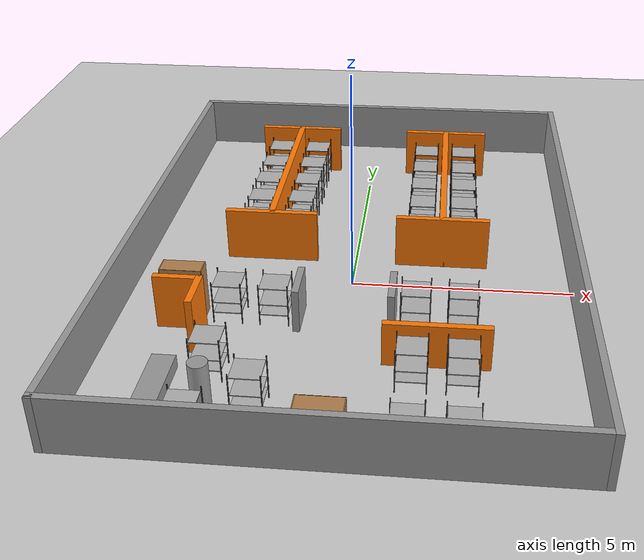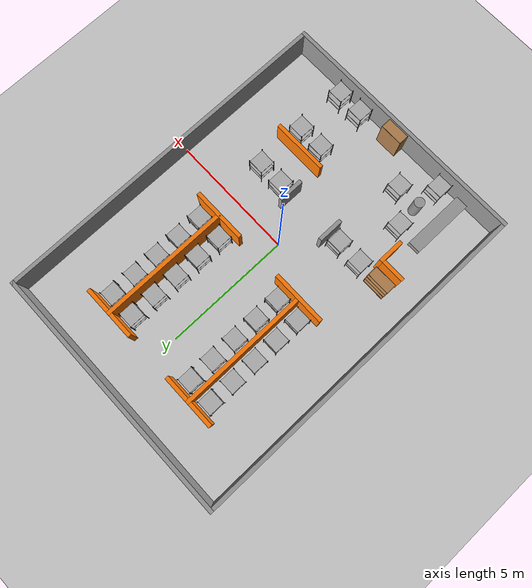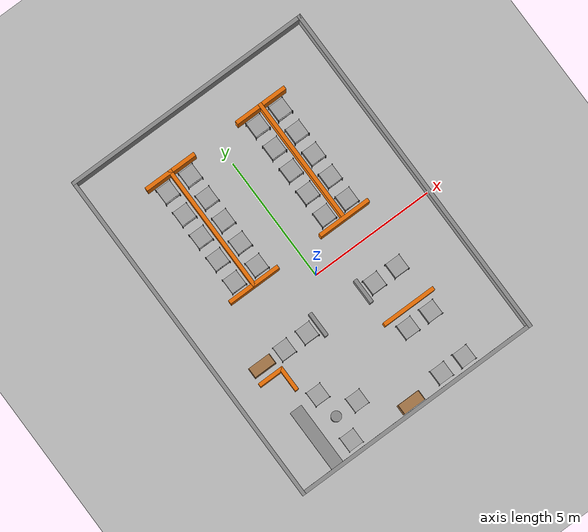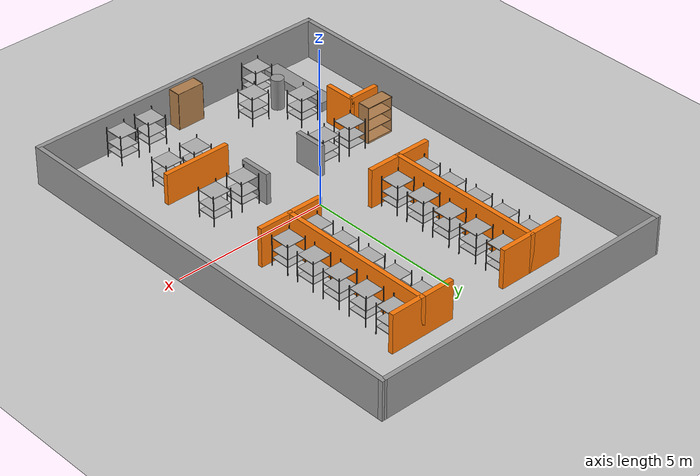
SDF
<sdf version="1.7">
 <world name="default">
  <light name="sun" type="directional">
   <pose>0 0 10 0 -0 0</pose>
   <diffuse>0.8 0.8 0.8 1</diffuse>
   <specular>0.2 0.2 0.2 1</specular>
   <attenuation>
    <range>1000</range>
    <constant>0.9</constant>
    <linear>0.01</linear>
    <quadratic>0.001</quadratic>
   </attenuation>
   <direction>-0.5 0.1 -0.9</direction>
   <spot><inner_angle>0</inner_angle><outer_angle>0</outer_angle><falloff>0</falloff></spot>
  </light>
  <model name="ground_plane">
   <static>1</static>
   <link name="link">
    <collision name="collision">
     <geometry><plane><normal>0 0 1</normal><size>100 100</size></plane></geometry>
     <surface><friction><ode><mu>100</mu><mu2>50</mu2></ode></friction></surface>
    </collision>
    <visual name="visual">
     <cast_shadows>0</cast_shadows>
     <geometry><plane><normal>0 0 1</normal><size>100 100</size></plane></geometry>
     <material>
      <script><uri>file://media/materials/scripts/gazebo.material</uri><name>Gazebo/Grey</name></script>
     </material>
    </visual>
   </link>
  </model>
  <gravity>0 0 -9.8</gravity>
  <magnetic_field>6e-06 2.3e-05 -4.2e-05</magnetic_field>
  <atmosphere type="adiabatic"/>
  <physics type="ode">
   <max_step_size>0.001</max_step_size>
   <real_time_factor>1</real_time_factor>
   <real_time_update_rate>1000</real_time_update_rate>
  </physics>
  <scene><ambient>0.4 0.4 0.4 1</ambient><background>0.7 0.7 0.7 1</background><shadows>1</shadows></scene>
  <audio><device>default</device></audio>
  <spherical_coordinates>
   <surface_model>EARTH_WGS84</surface_model>
   <latitude_deg>0</latitude_deg>
   <longitude_deg>0</longitude_deg>
   <elevation>0</elevation>
   <heading_deg>0</heading_deg>
  </spherical_coordinates>
  <model name="simple_shelf">
   <link name="link">
    <visual name="bottom_shelf_visual">
     <geometry><box><size>0.6 0.6 0.02</size></box></geometry>
     <pose>0 0 0.25 0 -0 0</pose>
     <material><ambient>0.6 0.6 0.6 1</ambient><diffuse>0.7 0.7 0.7 1</diffuse></material>
    </visual>
    <collision name="bottom_shelf_collision">
     <geometry><box><size>0.6 0.6 0.02</size></box></geometry>
     <pose>0 0 0.25 0 -0 0</pose>
    </collision>
    <visual name="middle_shelf_visual">
     <geometry><box><size>0.6 0.6 0.02</size></box></geometry>
     <pose>0 0 0.5 0 -0 0</pose>
     <material><ambient>0.6 0.6 0.6 1</ambient><diffuse>0.7 0.7 0.7 1</diffuse></material>
    </visual>
    <collision name="middle_shelf_collision">
     <geometry><box><size>0.6 0.6 0.02</size></box></geometry>
     <pose>0 0 0.5 0 -0 0</pose>
    </collision>
    <visual name="top_shelf_visual">
     <geometry><box><size>0.6 0.6 0.02</size></box></geometry>
     <pose>0 0 0.9 0 -0 0</pose>
     <material><ambient>0.6 0.6 0.6 1</ambient><diffuse>0.7 0.7 0.7 1</diffuse></material>
    </visual>
    <collision name="top_shelf_collision">
     <geometry><box><size>0.6 0.6 0.02</size></box></geometry>
     <pose>0 0 0.9 0 -0 0</pose>
    </collision>
    <visual name="left_support_visual">
     <geometry><box><size>0.02 0.02 1</size></box></geometry>
     <pose>-0.31 -0.31 0.5 0 -0 0</pose>
     <material><ambient>0.3 0.3 0.3 1</ambient><diffuse>0.3 0.3 0.3 1</diffuse></material>
    </visual>
    <collision name="left_support_collision">
     <geometry><box><size>0.02 0.02 1</size></box></geometry>
     <pose>-0.31 -0.31 0.5 0 -0 0</pose>
    </collision>
    <visual name="right_support_visual">
     <geometry><box><size>0.02 0.02 1</size></box></geometry>
     <pose>0.31 -0.31 0.5 0 -0 0</pose>
     <material><ambient>0.3 0.3 0.3 1</ambient><diffuse>0.3 0.3 0.3 1</diffuse></material>
    </visual>
    <collision name="right_support_collision">
     <geometry><box><size>0.02 0.02 1</size></box></geometry>
     <pose>0.31 -0.31 0.5 0 -0 0</pose>
    </collision>
    <visual name="front_left_support_visual">
     <geometry><box><size>0.02 0.02 1</size></box></geometry>
     <pose>-0.31 0.31 0.5 0 -0 0</pose>
     <material><ambient>0.3 0.3 0.3 1</ambient><diffuse>0.3 0.3 0.3 1</diffuse></material>
    </visual>
    <collision name="front_left_support_collision">
     <geometry><box><size>0.02 0.02 1</size></box></geometry>
     <pose>-0.31 0.31 0.5 0 -0 0</pose>
    </collision>
    <visual name="front_right_support_visual">
     <geometry><box><size>0.02 0.02 1</size></box></geometry>
     <pose>0.31 0.31 0.5 0 -0 0</pose>
     <material><ambient>0.3 0.3 0.3 1</ambient><diffuse>0.3 0.3 0.3 1</diffuse></material>
    </visual>
    <collision name="front_right_support_collision">
     <geometry><box><size>0.02 0.02 1</size></box></geometry>
     <pose>0.31 0.31 0.5 0 -0 0</pose>
    </collision>
    <inertial>
     <inertia><ixx>1</ixx><ixy>0</ixy><ixz>0</ixz><iyy>1</iyy><iyz>0</iyz><izz>1</izz></inertia>
     <mass>1</mass>
    </inertial>
   </link>
   <pose>-1.5 1.5 -1e-06 -1e-06 -1e-06 0</pose>
  </model>
  <model name="simple_shelf_0">
   <link name="link">
    <visual name="bottom_shelf_visual">
     <geometry><box><size>0.6 0.6 0.02</size></box></geometry>
     <pose>0 0 0.25 0 -0 0</pose>
     <material><ambient>0.6 0.6 0.6 1</ambient><diffuse>0.7 0.7 0.7 1</diffuse></material>
    </visual>
    <collision name="bottom_shelf_collision">
     <geometry><box><size>0.6 0.6 0.02</size></box></geometry>
     <pose>0 0 0.25 0 -0 0</pose>
    </collision>
    <visual name="middle_shelf_visual">
     <geometry><box><size>0.6 0.6 0.02</size></box></geometry>
     <pose>0 0 0.5 0 -0 0</pose>
     <material><ambient>0.6 0.6 0.6 1</ambient><diffuse>0.7 0.7 0.7 1</diffuse></material>
    </visual>
    <collision name="middle_shelf_collision">
     <geometry><box><size>0.6 0.6 0.02</size></box></geometry>
     <pose>0 0 0.5 0 -0 0</pose>
    </collision>
    <visual name="top_shelf_visual">
     <geometry><box><size>0.6 0.6 0.02</size></box></geometry>
     <pose>0 0 0.9 0 -0 0</pose>
     <material><ambient>0.6 0.6 0.6 1</ambient><diffuse>0.7 0.7 0.7 1</diffuse></material>
    </visual>
    <collision name="top_shelf_collision">
     <geometry><box><size>0.6 0.6 0.02</size></box></geometry>
     <pose>0 0 0.9 0 -0 0</pose>
    </collision>
    <visual name="left_support_visual">
     <geometry><box><size>0.02 0.02 1</size></box></geometry>
     <pose>-0.31 -0.31 0.5 0 -0 0</pose>
     <material><ambient>0.3 0.3 0.3 1</ambient><diffuse>0.3 0.3 0.3 1</diffuse></material>
    </visual>
    <collision name="left_support_collision">
     <geometry><box><size>0.02 0.02 1</size></box></geometry>
     <pose>-0.31 -0.31 0.5 0 -0 0</pose>
    </collision>
    <visual name="right_support_visual">
     <geometry><box><size>0.02 0.02 1</size></box></geometry>
     <pose>0.31 -0.31 0.5 0 -0 0</pose>
     <material><ambient>0.3 0.3 0.3 1</ambient><diffuse>0.3 0.3 0.3 1</diffuse></material>
    </visual>
    <collision name="right_support_collision">
     <geometry><box><size>0.02 0.02 1</size></box></geometry>
     <pose>0.31 -0.31 0.5 0 -0 0</pose>
    </collision>
    <visual name="front_left_support_visual">
     <geometry><box><size>0.02 0.02 1</size></box></geometry>
     <pose>-0.31 0.31 0.5 0 -0 0</pose>
     <material><ambient>0.3 0.3 0.3 1</ambient><diffuse>0.3 0.3 0.3 1</diffuse></material>
    </visual>
    <collision name="front_left_support_collision">
     <geometry><box><size>0.02 0.02 1</size></box></geometry>
     <pose>-0.31 0.31 0.5 0 -0 0</pose>
    </collision>
    <visual name="front_right_support_visual">
     <geometry><box><size>0.02 0.02 1</size></box></geometry>
     <pose>0.31 0.31 0.5 0 -0 0</pose>
     <material><ambient>0.3 0.3 0.3 1</ambient><diffuse>0.3 0.3 0.3 1</diffuse></material>
    </visual>
    <collision name="front_right_support_collision">
     <geometry><box><size>0.02 0.02 1</size></box></geometry>
     <pose>0.31 0.31 0.5 0 -0 0</pose>
    </collision>
    <inertial>
     <inertia><ixx>1</ixx><ixy>0</ixy><ixz>0</ixz><iyy>1</iyy><iyz>0</iyz><izz>1</izz></inertia>
     <mass>1</mass>
    </inertial>
   </link>
   <pose>-2.5 1.5 -1e-06 -1e-06 -1e-06 0</pose>
  </model>
  <model name="simple_shelf_1">
   <link name="link">
    <visual name="bottom_shelf_visual">
     <geometry><box><size>0.6 0.6 0.02</size></box></geometry>
     <pose>0 0 0.25 0 -0 0</pose>
     <material><ambient>0.6 0.6 0.6 1</ambient><diffuse>0.7 0.7 0.7 1</diffuse></material>
    </visual>
    <collision name="bottom_shelf_collision">
     <geometry><box><size>0.6 0.6 0.02</size></box></geometry>
     <pose>0 0 0.25 0 -0 0</pose>
    </collision>
    <visual name="middle_shelf_visual">
     <geometry><box><size>0.6 0.6 0.02</size></box></geometry>
     <pose>0 0 0.5 0 -0 0</pose>
     <material><ambient>0.6 0.6 0.6 1</ambient><diffuse>0.7 0.7 0.7 1</diffuse></material>
    </visual>
    <collision name="middle_shelf_collision">
     <geometry><box><size>0.6 0.6 0.02</size></box></geometry>
     <pose>0 0 0.5 0 -0 0</pose>
    </collision>
    <visual name="top_shelf_visual">
     <geometry><box><size>0.6 0.6 0.02</size></box></geometry>
     <pose>0 0 0.9 0 -0 0</pose>
     <material><ambient>0.6 0.6 0.6 1</ambient><diffuse>0.7 0.7 0.7 1</diffuse></material>
    </visual>
    <collision name="top_shelf_collision">
     <geometry><box><size>0.6 0.6 0.02</size></box></geometry>
     <pose>0 0 0.9 0 -0 0</pose>
    </collision>
    <visual name="left_support_visual">
     <geometry><box><size>0.02 0.02 1</size></box></geometry>
     <pose>-0.31 -0.31 0.5 0 -0 0</pose>
     <material><ambient>0.3 0.3 0.3 1</ambient><diffuse>0.3 0.3 0.3 1</diffuse></material>
    </visual>
    <collision name="left_support_collision">
     <geometry><box><size>0.02 0.02 1</size></box></geometry>
     <pose>-0.31 -0.31 0.5 0 -0 0</pose>
    </collision>
    <visual name="right_support_visual">
     <geometry><box><size>0.02 0.02 1</size></box></geometry>
     <pose>0.31 -0.31 0.5 0 -0 0</pose>
     <material><ambient>0.3 0.3 0.3 1</ambient><diffuse>0.3 0.3 0.3 1</diffuse></material>
    </visual>
    <collision name="right_support_collision">
     <geometry><box><size>0.02 0.02 1</size></box></geometry>
     <pose>0.31 -0.31 0.5 0 -0 0</pose>
    </collision>
    <visual name="front_left_support_visual">
     <geometry><box><size>0.02 0.02 1</size></box></geometry>
     <pose>-0.31 0.31 0.5 0 -0 0</pose>
     <material><ambient>0.3 0.3 0.3 1</ambient><diffuse>0.3 0.3 0.3 1</diffuse></material>
    </visual>
    <collision name="front_left_support_collision">
     <geometry><box><size>0.02 0.02 1</size></box></geometry>
     <pose>-0.31 0.31 0.5 0 -0 0</pose>
    </collision>
    <visual name="front_right_support_visual">
     <geometry><box><size>0.02 0.02 1</size></box></geometry>
     <pose>0.31 0.31 0.5 0 -0 0</pose>
     <material><ambient>0.3 0.3 0.3 1</ambient><diffuse>0.3 0.3 0.3 1</diffuse></material>
    </visual>
    <collision name="front_right_support_collision">
     <geometry><box><size>0.02 0.02 1</size></box></geometry>
     <pose>0.31 0.31 0.5 0 -0 0</pose>
    </collision>
    <inertial>
     <inertia><ixx>1</ixx><ixy>0</ixy><ixz>0</ixz><iyy>1</iyy><iyz>0</iyz><izz>1</izz></inertia>
     <mass>1</mass>
    </inertial>
   </link>
   <pose>1.5 1.5 -1e-06 -1e-06 -1e-06 0</pose>
  </model>
  <model name="simple_shelf_2">
   <link name="link">
    <visual name="bottom_shelf_visual">
     <geometry><box><size>0.6 0.6 0.02</size></box></geometry>
     <pose>0 0 0.25 0 -0 0</pose>
     <material><ambient>0.6 0.6 0.6 1</ambient><diffuse>0.7 0.7 0.7 1</diffuse></material>
    </visual>
    <collision name="bottom_shelf_collision">
     <geometry><box><size>0.6 0.6 0.02</size></box></geometry>
     <pose>0 0 0.25 0 -0 0</pose>
    </collision>
    <visual name="middle_shelf_visual">
     <geometry><box><size>0.6 0.6 0.02</size></box></geometry>
     <pose>0 0 0.5 0 -0 0</pose>
     <material><ambient>0.6 0.6 0.6 1</ambient><diffuse>0.7 0.7 0.7 1</diffuse></material>
    </visual>
    <collision name="middle_shelf_collision">
     <geometry><box><size>0.6 0.6 0.02</size></box></geometry>
     <pose>0 0 0.5 0 -0 0</pose>
    </collision>
    <visual name="top_shelf_visual">
     <geometry><box><size>0.6 0.6 0.02</size></box></geometry>
     <pose>0 0 0.9 0 -0 0</pose>
     <material><ambient>0.6 0.6 0.6 1</ambient><diffuse>0.7 0.7 0.7 1</diffuse></material>
    </visual>
    <collision name="top_shelf_collision">
     <geometry><box><size>0.6 0.6 0.02</size></box></geometry>
     <pose>0 0 0.9 0 -0 0</pose>
    </collision>
    <visual name="left_support_visual">
     <geometry><box><size>0.02 0.02 1</size></box></geometry>
     <pose>-0.31 -0.31 0.5 0 -0 0</pose>
     <material><ambient>0.3 0.3 0.3 1</ambient><diffuse>0.3 0.3 0.3 1</diffuse></material>
    </visual>
    <collision name="left_support_collision">
     <geometry><box><size>0.02 0.02 1</size></box></geometry>
     <pose>-0.31 -0.31 0.5 0 -0 0</pose>
    </collision>
    <visual name="right_support_visual">
     <geometry><box><size>0.02 0.02 1</size></box></geometry>
     <pose>0.31 -0.31 0.5 0 -0 0</pose>
     <material><ambient>0.3 0.3 0.3 1</ambient><diffuse>0.3 0.3 0.3 1</diffuse></material>
    </visual>
    <collision name="right_support_collision">
     <geometry><box><size>0.02 0.02 1</size></box></geometry>
     <pose>0.31 -0.31 0.5 0 -0 0</pose>
    </collision>
    <visual name="front_left_support_visual">
     <geometry><box><size>0.02 0.02 1</size></box></geometry>
     <pose>-0.31 0.31 0.5 0 -0 0</pose>
     <material><ambient>0.3 0.3 0.3 1</ambient><diffuse>0.3 0.3 0.3 1</diffuse></material>
    </visual>
    <collision name="front_left_support_collision">
     <geometry><box><size>0.02 0.02 1</size></box></geometry>
     <pose>-0.31 0.31 0.5 0 -0 0</pose>
    </collision>
    <visual name="front_right_support_visual">
     <geometry><box><size>0.02 0.02 1</size></box></geometry>
     <pose>0.31 0.31 0.5 0 -0 0</pose>
     <material><ambient>0.3 0.3 0.3 1</ambient><diffuse>0.3 0.3 0.3 1</diffuse></material>
    </visual>
    <collision name="front_right_support_collision">
     <geometry><box><size>0.02 0.02 1</size></box></geometry>
     <pose>0.31 0.31 0.5 0 -0 0</pose>
    </collision>
    <inertial>
     <inertia><ixx>1</ixx><ixy>0</ixy><ixz>0</ixz><iyy>1</iyy><iyz>0</iyz><izz>1</izz></inertia>
     <mass>1</mass>
    </inertial>
   </link>
   <pose>2.5 1.5 -1e-06 -1e-06 -1e-06 0</pose>
  </model>
  <model name="simple_shelf_3">
   <link name="link">
    <visual name="bottom_shelf_visual">
     <geometry><box><size>0.6 0.6 0.02</size></box></geometry>
     <pose>0 0 0.25 0 -0 0</pose>
     <material><ambient>0.6 0.6 0.6 1</ambient><diffuse>0.7 0.7 0.7 1</diffuse></material>
    </visual>
    <collision name="bottom_shelf_collision">
     <geometry><box><size>0.6 0.6 0.02</size></box></geometry>
     <pose>0 0 0.25 0 -0 0</pose>
    </collision>
    <visual name="middle_shelf_visual">
     <geometry><box><size>0.6 0.6 0.02</size></box></geometry>
     <pose>0 0 0.5 0 -0 0</pose>
     <material><ambient>0.6 0.6 0.6 1</ambient><diffuse>0.7 0.7 0.7 1</diffuse></material>
    </visual>
    <collision name="middle_shelf_collision">
     <geometry><box><size>0.6 0.6 0.02</size></box></geometry>
     <pose>0 0 0.5 0 -0 0</pose>
    </collision>
    <visual name="top_shelf_visual">
     <geometry><box><size>0.6 0.6 0.02</size></box></geometry>
     <pose>0 0 0.9 0 -0 0</pose>
     <material><ambient>0.6 0.6 0.6 1</ambient><diffuse>0.7 0.7 0.7 1</diffuse></material>
    </visual>
    <collision name="top_shelf_collision">
     <geometry><box><size>0.6 0.6 0.02</size></box></geometry>
     <pose>0 0 0.9 0 -0 0</pose>
    </collision>
    <visual name="left_support_visual">
     <geometry><box><size>0.02 0.02 1</size></box></geometry>
     <pose>-0.31 -0.31 0.5 0 -0 0</pose>
     <material><ambient>0.3 0.3 0.3 1</ambient><diffuse>0.3 0.3 0.3 1</diffuse></material>
    </visual>
    <collision name="left_support_collision">
     <geometry><box><size>0.02 0.02 1</size></box></geometry>
     <pose>-0.31 -0.31 0.5 0 -0 0</pose>
    </collision>
    <visual name="right_support_visual">
     <geometry><box><size>0.02 0.02 1</size></box></geometry>
     <pose>0.31 -0.31 0.5 0 -0 0</pose>
     <material><ambient>0.3 0.3 0.3 1</ambient><diffuse>0.3 0.3 0.3 1</diffuse></material>
    </visual>
    <collision name="right_support_collision">
     <geometry><box><size>0.02 0.02 1</size></box></geometry>
     <pose>0.31 -0.31 0.5 0 -0 0</pose>
    </collision>
    <visual name="front_left_support_visual">
     <geometry><box><size>0.02 0.02 1</size></box></geometry>
     <pose>-0.31 0.31 0.5 0 -0 0</pose>
     <material><ambient>0.3 0.3 0.3 1</ambient><diffuse>0.3 0.3 0.3 1</diffuse></material>
    </visual>
    <collision name="front_left_support_collision">
     <geometry><box><size>0.02 0.02 1</size></box></geometry>
     <pose>-0.31 0.31 0.5 0 -0 0</pose>
    </collision>
    <visual name="front_right_support_visual">
     <geometry><box><size>0.02 0.02 1</size></box></geometry>
     <pose>0.31 0.31 0.5 0 -0 0</pose>
     <material><ambient>0.3 0.3 0.3 1</ambient><diffuse>0.3 0.3 0.3 1</diffuse></material>
    </visual>
    <collision name="front_right_support_collision">
     <geometry><box><size>0.02 0.02 1</size></box></geometry>
     <pose>0.31 0.31 0.5 0 -0 0</pose>
    </collision>
    <inertial>
     <inertia><ixx>1</ixx><ixy>0</ixy><ixz>0</ixz><iyy>1</iyy><iyz>0</iyz><izz>1</izz></inertia>
     <mass>1</mass>
    </inertial>
   </link>
   <pose>-1.5 2.5 -1e-06 -1e-06 -1e-06 0</pose>
  </model>
  <model name="simple_shelf_4">
   <link name="link">
    <visual name="bottom_shelf_visual">
     <geometry><box><size>0.6 0.6 0.02</size></box></geometry>
     <pose>0 0 0.25 0 -0 0</pose>
     <material><ambient>0.6 0.6 0.6 1</ambient><diffuse>0.7 0.7 0.7 1</diffuse></material>
    </visual>
    <collision name="bottom_shelf_collision">
     <geometry><box><size>0.6 0.6 0.02</size></box></geometry>
     <pose>0 0 0.25 0 -0 0</pose>
    </collision>
    <visual name="middle_shelf_visual">
     <geometry><box><size>0.6 0.6 0.02</size></box></geometry>
     <pose>0 0 0.5 0 -0 0</pose>
     <material><ambient>0.6 0.6 0.6 1</ambient><diffuse>0.7 0.7 0.7 1</diffuse></material>
    </visual>
    <collision name="middle_shelf_collision">
     <geometry><box><size>0.6 0.6 0.02</size></box></geometry>
     <pose>0 0 0.5 0 -0 0</pose>
    </collision>
    <visual name="top_shelf_visual">
     <geometry><box><size>0.6 0.6 0.02</size></box></geometry>
     <pose>0 0 0.9 0 -0 0</pose>
     <material><ambient>0.6 0.6 0.6 1</ambient><diffuse>0.7 0.7 0.7 1</diffuse></material>
    </visual>
    <collision name="top_shelf_collision">
     <geometry><box><size>0.6 0.6 0.02</size></box></geometry>
     <pose>0 0 0.9 0 -0 0</pose>
    </collision>
    <visual name="left_support_visual">
     <geometry><box><size>0.02 0.02 1</size></box></geometry>
     <pose>-0.31 -0.31 0.5 0 -0 0</pose>
     <material><ambient>0.3 0.3 0.3 1</ambient><diffuse>0.3 0.3 0.3 1</diffuse></material>
    </visual>
    <collision name="left_support_collision">
     <geometry><box><size>0.02 0.02 1</size></box></geometry>
     <pose>-0.31 -0.31 0.5 0 -0 0</pose>
    </collision>
    <visual name="right_support_visual">
     <geometry><box><size>0.02 0.02 1</size></box></geometry>
     <pose>0.31 -0.31 0.5 0 -0 0</pose>
     <material><ambient>0.3 0.3 0.3 1</ambient><diffuse>0.3 0.3 0.3 1</diffuse></material>
    </visual>
    <collision name="right_support_collision">
     <geometry><box><size>0.02 0.02 1</size></box></geometry>
     <pose>0.31 -0.31 0.5 0 -0 0</pose>
    </collision>
    <visual name="front_left_support_visual">
     <geometry><box><size>0.02 0.02 1</size></box></geometry>
     <pose>-0.31 0.31 0.5 0 -0 0</pose>
     <material><ambient>0.3 0.3 0.3 1</ambient><diffuse>0.3 0.3 0.3 1</diffuse></material>
    </visual>
    <collision name="front_left_support_collision">
     <geometry><box><size>0.02 0.02 1</size></box></geometry>
     <pose>-0.31 0.31 0.5 0 -0 0</pose>
    </collision>
    <visual name="front_right_support_visual">
     <geometry><box><size>0.02 0.02 1</size></box></geometry>
     <pose>0.31 0.31 0.5 0 -0 0</pose>
     <material><ambient>0.3 0.3 0.3 1</ambient><diffuse>0.3 0.3 0.3 1</diffuse></material>
    </visual>
    <collision name="front_right_support_collision">
     <geometry><box><size>0.02 0.02 1</size></box></geometry>
     <pose>0.31 0.31 0.5 0 -0 0</pose>
    </collision>
    <inertial>
     <inertia><ixx>1</ixx><ixy>0</ixy><ixz>0</ixz><iyy>1</iyy><iyz>0</iyz><izz>1</izz></inertia>
     <mass>1</mass>
    </inertial>
   </link>
   <pose>-1.5 3.5 -1e-06 -1e-06 -1e-06 0</pose>
  </model>
  <model name="simple_shelf_5">
   <link name="link">
    <visual name="bottom_shelf_visual">
     <geometry><box><size>0.6 0.6 0.02</size></box></geometry>
     <pose>0 0 0.25 0 -0 0</pose>
     <material><ambient>0.6 0.6 0.6 1</ambient><diffuse>0.7 0.7 0.7 1</diffuse></material>
    </visual>
    <collision name="bottom_shelf_collision">
     <geometry><box><size>0.6 0.6 0.02</size></box></geometry>
     <pose>0 0 0.25 0 -0 0</pose>
    </collision>
    <visual name="middle_shelf_visual">
     <geometry><box><size>0.6 0.6 0.02</size></box></geometry>
     <pose>0 0 0.5 0 -0 0</pose>
     <material><ambient>0.6 0.6 0.6 1</ambient><diffuse>0.7 0.7 0.7 1</diffuse></material>
    </visual>
    <collision name="middle_shelf_collision">
     <geometry><box><size>0.6 0.6 0.02</size></box></geometry>
     <pose>0 0 0.5 0 -0 0</pose>
    </collision>
    <visual name="top_shelf_visual">
     <geometry><box><size>0.6 0.6 0.02</size></box></geometry>
     <pose>0 0 0.9 0 -0 0</pose>
     <material><ambient>0.6 0.6 0.6 1</ambient><diffuse>0.7 0.7 0.7 1</diffuse></material>
    </visual>
    <collision name="top_shelf_collision">
     <geometry><box><size>0.6 0.6 0.02</size></box></geometry>
     <pose>0 0 0.9 0 -0 0</pose>
    </collision>
    <visual name="left_support_visual">
     <geometry><box><size>0.02 0.02 1</size></box></geometry>
     <pose>-0.31 -0.31 0.5 0 -0 0</pose>
     <material><ambient>0.3 0.3 0.3 1</ambient><diffuse>0.3 0.3 0.3 1</diffuse></material>
    </visual>
    <collision name="left_support_collision">
     <geometry><box><size>0.02 0.02 1</size></box></geometry>
     <pose>-0.31 -0.31 0.5 0 -0 0</pose>
    </collision>
    <visual name="right_support_visual">
     <geometry><box><size>0.02 0.02 1</size></box></geometry>
     <pose>0.31 -0.31 0.5 0 -0 0</pose>
     <material><ambient>0.3 0.3 0.3 1</ambient><diffuse>0.3 0.3 0.3 1</diffuse></material>
    </visual>
    <collision name="right_support_collision">
     <geometry><box><size>0.02 0.02 1</size></box></geometry>
     <pose>0.31 -0.31 0.5 0 -0 0</pose>
    </collision>
    <visual name="front_left_support_visual">
     <geometry><box><size>0.02 0.02 1</size></box></geometry>
     <pose>-0.31 0.31 0.5 0 -0 0</pose>
     <material><ambient>0.3 0.3 0.3 1</ambient><diffuse>0.3 0.3 0.3 1</diffuse></material>
    </visual>
    <collision name="front_left_support_collision">
     <geometry><box><size>0.02 0.02 1</size></box></geometry>
     <pose>-0.31 0.31 0.5 0 -0 0</pose>
    </collision>
    <visual name="front_right_support_visual">
     <geometry><box><size>0.02 0.02 1</size></box></geometry>
     <pose>0.31 0.31 0.5 0 -0 0</pose>
     <material><ambient>0.3 0.3 0.3 1</ambient><diffuse>0.3 0.3 0.3 1</diffuse></material>
    </visual>
    <collision name="front_right_support_collision">
     <geometry><box><size>0.02 0.02 1</size></box></geometry>
     <pose>0.31 0.31 0.5 0 -0 0</pose>
    </collision>
    <inertial>
     <inertia><ixx>1</ixx><ixy>0</ixy><ixz>0</ixz><iyy>1</iyy><iyz>0</iyz><izz>1</izz></inertia>
     <mass>1</mass>
    </inertial>
   </link>
   <pose>-1.5 4.5 -1e-06 -1e-06 -1e-06 0</pose>
  </model>
  <model name="simple_shelf_6">
   <link name="link">
    <visual name="bottom_shelf_visual">
     <geometry><box><size>0.6 0.6 0.02</size></box></geometry>
     <pose>0 0 0.25 0 -0 0</pose>
     <material><ambient>0.6 0.6 0.6 1</ambient><diffuse>0.7 0.7 0.7 1</diffuse></material>
    </visual>
    <collision name="bottom_shelf_collision">
     <geometry><box><size>0.6 0.6 0.02</size></box></geometry>
     <pose>0 0 0.25 0 -0 0</pose>
    </collision>
    <visual name="middle_shelf_visual">
     <geometry><box><size>0.6 0.6 0.02</size></box></geometry>
     <pose>0 0 0.5 0 -0 0</pose>
     <material><ambient>0.6 0.6 0.6 1</ambient><diffuse>0.7 0.7 0.7 1</diffuse></material>
    </visual>
    <collision name="middle_shelf_collision">
     <geometry><box><size>0.6 0.6 0.02</size></box></geometry>
     <pose>0 0 0.5 0 -0 0</pose>
    </collision>
    <visual name="top_shelf_visual">
     <geometry><box><size>0.6 0.6 0.02</size></box></geometry>
     <pose>0 0 0.9 0 -0 0</pose>
     <material><ambient>0.6 0.6 0.6 1</ambient><diffuse>0.7 0.7 0.7 1</diffuse></material>
    </visual>
    <collision name="top_shelf_collision">
     <geometry><box><size>0.6 0.6 0.02</size></box></geometry>
     <pose>0 0 0.9 0 -0 0</pose>
    </collision>
    <visual name="left_support_visual">
     <geometry><box><size>0.02 0.02 1</size></box></geometry>
     <pose>-0.31 -0.31 0.5 0 -0 0</pose>
     <material><ambient>0.3 0.3 0.3 1</ambient><diffuse>0.3 0.3 0.3 1</diffuse></material>
    </visual>
    <collision name="left_support_collision">
     <geometry><box><size>0.02 0.02 1</size></box></geometry>
     <pose>-0.31 -0.31 0.5 0 -0 0</pose>
    </collision>
    <visual name="right_support_visual">
     <geometry><box><size>0.02 0.02 1</size></box></geometry>
     <pose>0.31 -0.31 0.5 0 -0 0</pose>
     <material><ambient>0.3 0.3 0.3 1</ambient><diffuse>0.3 0.3 0.3 1</diffuse></material>
    </visual>
    <collision name="right_support_collision">
     <geometry><box><size>0.02 0.02 1</size></box></geometry>
     <pose>0.31 -0.31 0.5 0 -0 0</pose>
    </collision>
    <visual name="front_left_support_visual">
     <geometry><box><size>0.02 0.02 1</size></box></geometry>
     <pose>-0.31 0.31 0.5 0 -0 0</pose>
     <material><ambient>0.3 0.3 0.3 1</ambient><diffuse>0.3 0.3 0.3 1</diffuse></material>
    </visual>
    <collision name="front_left_support_collision">
     <geometry><box><size>0.02 0.02 1</size></box></geometry>
     <pose>-0.31 0.31 0.5 0 -0 0</pose>
    </collision>
    <visual name="front_right_support_visual">
     <geometry><box><size>0.02 0.02 1</size></box></geometry>
     <pose>0.31 0.31 0.5 0 -0 0</pose>
     <material><ambient>0.3 0.3 0.3 1</ambient><diffuse>0.3 0.3 0.3 1</diffuse></material>
    </visual>
    <collision name="front_right_support_collision">
     <geometry><box><size>0.02 0.02 1</size></box></geometry>
     <pose>0.31 0.31 0.5 0 -0 0</pose>
    </collision>
    <inertial>
     <inertia><ixx>1</ixx><ixy>0</ixy><ixz>0</ixz><iyy>1</iyy><iyz>0</iyz><izz>1</izz></inertia>
     <mass>1</mass>
    </inertial>
   </link>
   <pose>-1.5 5.5 -1e-06 -1e-06 -1e-06 0</pose>
  </model>
  <model name="simple_shelf_7">
   <link name="link">
    <visual name="bottom_shelf_visual">
     <geometry><box><size>0.6 0.6 0.02</size></box></geometry>
     <pose>0 0 0.25 0 -0 0</pose>
     <material><ambient>0.6 0.6 0.6 1</ambient><diffuse>0.7 0.7 0.7 1</diffuse></material>
    </visual>
    <collision name="bottom_shelf_collision">
     <geometry><box><size>0.6 0.6 0.02</size></box></geometry>
     <pose>0 0 0.25 0 -0 0</pose>
    </collision>
    <visual name="middle_shelf_visual">
     <geometry><box><size>0.6 0.6 0.02</size></box></geometry>
     <pose>0 0 0.5 0 -0 0</pose>
     <material><ambient>0.6 0.6 0.6 1</ambient><diffuse>0.7 0.7 0.7 1</diffuse></material>
    </visual>
    <collision name="middle_shelf_collision">
     <geometry><box><size>0.6 0.6 0.02</size></box></geometry>
     <pose>0 0 0.5 0 -0 0</pose>
    </collision>
    <visual name="top_shelf_visual">
     <geometry><box><size>0.6 0.6 0.02</size></box></geometry>
     <pose>0 0 0.9 0 -0 0</pose>
     <material><ambient>0.6 0.6 0.6 1</ambient><diffuse>0.7 0.7 0.7 1</diffuse></material>
    </visual>
    <collision name="top_shelf_collision">
     <geometry><box><size>0.6 0.6 0.02</size></box></geometry>
     <pose>0 0 0.9 0 -0 0</pose>
    </collision>
    <visual name="left_support_visual">
     <geometry><box><size>0.02 0.02 1</size></box></geometry>
     <pose>-0.31 -0.31 0.5 0 -0 0</pose>
     <material><ambient>0.3 0.3 0.3 1</ambient><diffuse>0.3 0.3 0.3 1</diffuse></material>
    </visual>
    <collision name="left_support_collision">
     <geometry><box><size>0.02 0.02 1</size></box></geometry>
     <pose>-0.31 -0.31 0.5 0 -0 0</pose>
    </collision>
    <visual name="right_support_visual">
     <geometry><box><size>0.02 0.02 1</size></box></geometry>
     <pose>0.31 -0.31 0.5 0 -0 0</pose>
     <material><ambient>0.3 0.3 0.3 1</ambient><diffuse>0.3 0.3 0.3 1</diffuse></material>
    </visual>
    <collision name="right_support_collision">
     <geometry><box><size>0.02 0.02 1</size></box></geometry>
     <pose>0.31 -0.31 0.5 0 -0 0</pose>
    </collision>
    <visual name="front_left_support_visual">
     <geometry><box><size>0.02 0.02 1</size></box></geometry>
     <pose>-0.31 0.31 0.5 0 -0 0</pose>
     <material><ambient>0.3 0.3 0.3 1</ambient><diffuse>0.3 0.3 0.3 1</diffuse></material>
    </visual>
    <collision name="front_left_support_collision">
     <geometry><box><size>0.02 0.02 1</size></box></geometry>
     <pose>-0.31 0.31 0.5 0 -0 0</pose>
    </collision>
    <visual name="front_right_support_visual">
     <geometry><box><size>0.02 0.02 1</size></box></geometry>
     <pose>0.31 0.31 0.5 0 -0 0</pose>
     <material><ambient>0.3 0.3 0.3 1</ambient><diffuse>0.3 0.3 0.3 1</diffuse></material>
    </visual>
    <collision name="front_right_support_collision">
     <geometry><box><size>0.02 0.02 1</size></box></geometry>
     <pose>0.31 0.31 0.5 0 -0 0</pose>
    </collision>
    <inertial>
     <inertia><ixx>1</ixx><ixy>0</ixy><ixz>0</ixz><iyy>1</iyy><iyz>0</iyz><izz>1</izz></inertia>
     <mass>1</mass>
    </inertial>
   </link>
   <pose>-2.5 2.5 -1e-06 -1e-06 -1e-06 0</pose>
  </model>
  <model name="simple_shelf_8">
   <link name="link">
    <visual name="bottom_shelf_visual">
     <geometry><box><size>0.6 0.6 0.02</size></box></geometry>
     <pose>0 0 0.25 0 -0 0</pose>
     <material><ambient>0.6 0.6 0.6 1</ambient><diffuse>0.7 0.7 0.7 1</diffuse></material>
    </visual>
    <collision name="bottom_shelf_collision">
     <geometry><box><size>0.6 0.6 0.02</size></box></geometry>
     <pose>0 0 0.25 0 -0 0</pose>
    </collision>
    <visual name="middle_shelf_visual">
     <geometry><box><size>0.6 0.6 0.02</size></box></geometry>
     <pose>0 0 0.5 0 -0 0</pose>
     <material><ambient>0.6 0.6 0.6 1</ambient><diffuse>0.7 0.7 0.7 1</diffuse></material>
    </visual>
    <collision name="middle_shelf_collision">
     <geometry><box><size>0.6 0.6 0.02</size></box></geometry>
     <pose>0 0 0.5 0 -0 0</pose>
    </collision>
    <visual name="top_shelf_visual">
     <geometry><box><size>0.6 0.6 0.02</size></box></geometry>
     <pose>0 0 0.9 0 -0 0</pose>
     <material><ambient>0.6 0.6 0.6 1</ambient><diffuse>0.7 0.7 0.7 1</diffuse></material>
    </visual>
    <collision name="top_shelf_collision">
     <geometry><box><size>0.6 0.6 0.02</size></box></geometry>
     <pose>0 0 0.9 0 -0 0</pose>
    </collision>
    <visual name="left_support_visual">
     <geometry><box><size>0.02 0.02 1</size></box></geometry>
     <pose>-0.31 -0.31 0.5 0 -0 0</pose>
     <material><ambient>0.3 0.3 0.3 1</ambient><diffuse>0.3 0.3 0.3 1</diffuse></material>
    </visual>
    <collision name="left_support_collision">
     <geometry><box><size>0.02 0.02 1</size></box></geometry>
     <pose>-0.31 -0.31 0.5 0 -0 0</pose>
    </collision>
    <visual name="right_support_visual">
     <geometry><box><size>0.02 0.02 1</size></box></geometry>
     <pose>0.31 -0.31 0.5 0 -0 0</pose>
     <material><ambient>0.3 0.3 0.3 1</ambient><diffuse>0.3 0.3 0.3 1</diffuse></material>
    </visual>
    <collision name="right_support_collision">
     <geometry><box><size>0.02 0.02 1</size></box></geometry>
     <pose>0.31 -0.31 0.5 0 -0 0</pose>
    </collision>
    <visual name="front_left_support_visual">
     <geometry><box><size>0.02 0.02 1</size></box></geometry>
     <pose>-0.31 0.31 0.5 0 -0 0</pose>
     <material><ambient>0.3 0.3 0.3 1</ambient><diffuse>0.3 0.3 0.3 1</diffuse></material>
    </visual>
    <collision name="front_left_support_collision">
     <geometry><box><size>0.02 0.02 1</size></box></geometry>
     <pose>-0.31 0.31 0.5 0 -0 0</pose>
    </collision>
    <visual name="front_right_support_visual">
     <geometry><box><size>0.02 0.02 1</size></box></geometry>
     <pose>0.31 0.31 0.5 0 -0 0</pose>
     <material><ambient>0.3 0.3 0.3 1</ambient><diffuse>0.3 0.3 0.3 1</diffuse></material>
    </visual>
    <collision name="front_right_support_collision">
     <geometry><box><size>0.02 0.02 1</size></box></geometry>
     <pose>0.31 0.31 0.5 0 -0 0</pose>
    </collision>
    <inertial>
     <inertia><ixx>1</ixx><ixy>0</ixy><ixz>0</ixz><iyy>1</iyy><iyz>0</iyz><izz>1</izz></inertia>
     <mass>1</mass>
    </inertial>
   </link>
   <pose>-2.5 3.5 -1e-06 -1e-06 -1e-06 0</pose>
  </model>
  <model name="simple_shelf_9">
   <link name="link">
    <visual name="bottom_shelf_visual">
     <geometry><box><size>0.6 0.6 0.02</size></box></geometry>
     <pose>0 0 0.25 0 -0 0</pose>
     <material><ambient>0.6 0.6 0.6 1</ambient><diffuse>0.7 0.7 0.7 1</diffuse></material>
    </visual>
    <collision name="bottom_shelf_collision">
     <geometry><box><size>0.6 0.6 0.02</size></box></geometry>
     <pose>0 0 0.25 0 -0 0</pose>
    </collision>
    <visual name="middle_shelf_visual">
     <geometry><box><size>0.6 0.6 0.02</size></box></geometry>
     <pose>0 0 0.5 0 -0 0</pose>
     <material><ambient>0.6 0.6 0.6 1</ambient><diffuse>0.7 0.7 0.7 1</diffuse></material>
    </visual>
    <collision name="middle_shelf_collision">
     <geometry><box><size>0.6 0.6 0.02</size></box></geometry>
     <pose>0 0 0.5 0 -0 0</pose>
    </collision>
    <visual name="top_shelf_visual">
     <geometry><box><size>0.6 0.6 0.02</size></box></geometry>
     <pose>0 0 0.9 0 -0 0</pose>
     <material><ambient>0.6 0.6 0.6 1</ambient><diffuse>0.7 0.7 0.7 1</diffuse></material>
    </visual>
    <collision name="top_shelf_collision">
     <geometry><box><size>0.6 0.6 0.02</size></box></geometry>
     <pose>0 0 0.9 0 -0 0</pose>
    </collision>
    <visual name="left_support_visual">
     <geometry><box><size>0.02 0.02 1</size></box></geometry>
     <pose>-0.31 -0.31 0.5 0 -0 0</pose>
     <material><ambient>0.3 0.3 0.3 1</ambient><diffuse>0.3 0.3 0.3 1</diffuse></material>
    </visual>
    <collision name="left_support_collision">
     <geometry><box><size>0.02 0.02 1</size></box></geometry>
     <pose>-0.31 -0.31 0.5 0 -0 0</pose>
    </collision>
    <visual name="right_support_visual">
     <geometry><box><size>0.02 0.02 1</size></box></geometry>
     <pose>0.31 -0.31 0.5 0 -0 0</pose>
     <material><ambient>0.3 0.3 0.3 1</ambient><diffuse>0.3 0.3 0.3 1</diffuse></material>
    </visual>
    <collision name="right_support_collision">
     <geometry><box><size>0.02 0.02 1</size></box></geometry>
     <pose>0.31 -0.31 0.5 0 -0 0</pose>
    </collision>
    <visual name="front_left_support_visual">
     <geometry><box><size>0.02 0.02 1</size></box></geometry>
     <pose>-0.31 0.31 0.5 0 -0 0</pose>
     <material><ambient>0.3 0.3 0.3 1</ambient><diffuse>0.3 0.3 0.3 1</diffuse></material>
    </visual>
    <collision name="front_left_support_collision">
     <geometry><box><size>0.02 0.02 1</size></box></geometry>
     <pose>-0.31 0.31 0.5 0 -0 0</pose>
    </collision>
    <visual name="front_right_support_visual">
     <geometry><box><size>0.02 0.02 1</size></box></geometry>
     <pose>0.31 0.31 0.5 0 -0 0</pose>
     <material><ambient>0.3 0.3 0.3 1</ambient><diffuse>0.3 0.3 0.3 1</diffuse></material>
    </visual>
    <collision name="front_right_support_collision">
     <geometry><box><size>0.02 0.02 1</size></box></geometry>
     <pose>0.31 0.31 0.5 0 -0 0</pose>
    </collision>
    <inertial>
     <inertia><ixx>1</ixx><ixy>0</ixy><ixz>0</ixz><iyy>1</iyy><iyz>0</iyz><izz>1</izz></inertia>
     <mass>1</mass>
    </inertial>
   </link>
   <pose>-2.5 4.5 -1e-06 -1e-06 -1e-06 0</pose>
  </model>
  <model name="simple_shelf_10">
   <link name="link">
    <visual name="bottom_shelf_visual">
     <geometry><box><size>0.6 0.6 0.02</size></box></geometry>
     <pose>0 0 0.25 0 -0 0</pose>
     <material><ambient>0.6 0.6 0.6 1</ambient><diffuse>0.7 0.7 0.7 1</diffuse></material>
    </visual>
    <collision name="bottom_shelf_collision">
     <geometry><box><size>0.6 0.6 0.02</size></box></geometry>
     <pose>0 0 0.25 0 -0 0</pose>
    </collision>
    <visual name="middle_shelf_visual">
     <geometry><box><size>0.6 0.6 0.02</size></box></geometry>
     <pose>0 0 0.5 0 -0 0</pose>
     <material><ambient>0.6 0.6 0.6 1</ambient><diffuse>0.7 0.7 0.7 1</diffuse></material>
    </visual>
    <collision name="middle_shelf_collision">
     <geometry><box><size>0.6 0.6 0.02</size></box></geometry>
     <pose>0 0 0.5 0 -0 0</pose>
    </collision>
    <visual name="top_shelf_visual">
     <geometry><box><size>0.6 0.6 0.02</size></box></geometry>
     <pose>0 0 0.9 0 -0 0</pose>
     <material><ambient>0.6 0.6 0.6 1</ambient><diffuse>0.7 0.7 0.7 1</diffuse></material>
    </visual>
    <collision name="top_shelf_collision">
     <geometry><box><size>0.6 0.6 0.02</size></box></geometry>
     <pose>0 0 0.9 0 -0 0</pose>
    </collision>
    <visual name="left_support_visual">
     <geometry><box><size>0.02 0.02 1</size></box></geometry>
     <pose>-0.31 -0.31 0.5 0 -0 0</pose>
     <material><ambient>0.3 0.3 0.3 1</ambient><diffuse>0.3 0.3 0.3 1</diffuse></material>
    </visual>
    <collision name="left_support_collision">
     <geometry><box><size>0.02 0.02 1</size></box></geometry>
     <pose>-0.31 -0.31 0.5 0 -0 0</pose>
    </collision>
    <visual name="right_support_visual">
     <geometry><box><size>0.02 0.02 1</size></box></geometry>
     <pose>0.31 -0.31 0.5 0 -0 0</pose>
     <material><ambient>0.3 0.3 0.3 1</ambient><diffuse>0.3 0.3 0.3 1</diffuse></material>
    </visual>
    <collision name="right_support_collision">
     <geometry><box><size>0.02 0.02 1</size></box></geometry>
     <pose>0.31 -0.31 0.5 0 -0 0</pose>
    </collision>
    <visual name="front_left_support_visual">
     <geometry><box><size>0.02 0.02 1</size></box></geometry>
     <pose>-0.31 0.31 0.5 0 -0 0</pose>
     <material><ambient>0.3 0.3 0.3 1</ambient><diffuse>0.3 0.3 0.3 1</diffuse></material>
    </visual>
    <collision name="front_left_support_collision">
     <geometry><box><size>0.02 0.02 1</size></box></geometry>
     <pose>-0.31 0.31 0.5 0 -0 0</pose>
    </collision>
    <visual name="front_right_support_visual">
     <geometry><box><size>0.02 0.02 1</size></box></geometry>
     <pose>0.31 0.31 0.5 0 -0 0</pose>
     <material><ambient>0.3 0.3 0.3 1</ambient><diffuse>0.3 0.3 0.3 1</diffuse></material>
    </visual>
    <collision name="front_right_support_collision">
     <geometry><box><size>0.02 0.02 1</size></box></geometry>
     <pose>0.31 0.31 0.5 0 -0 0</pose>
    </collision>
    <inertial>
     <inertia><ixx>1</ixx><ixy>0</ixy><ixz>0</ixz><iyy>1</iyy><iyz>0</iyz><izz>1</izz></inertia>
     <mass>1</mass>
    </inertial>
   </link>
   <pose>-2.5 5.5 -1e-06 -1e-06 -1e-06 0</pose>
  </model>
  <model name="simple_shelf_11">
   <link name="link">
    <visual name="bottom_shelf_visual">
     <geometry><box><size>0.6 0.6 0.02</size></box></geometry>
     <pose>0 0 0.25 0 -0 0</pose>
     <material><ambient>0.6 0.6 0.6 1</ambient><diffuse>0.7 0.7 0.7 1</diffuse></material>
    </visual>
    <collision name="bottom_shelf_collision">
     <geometry><box><size>0.6 0.6 0.02</size></box></geometry>
     <pose>0 0 0.25 0 -0 0</pose>
    </collision>
    <visual name="middle_shelf_visual">
     <geometry><box><size>0.6 0.6 0.02</size></box></geometry>
     <pose>0 0 0.5 0 -0 0</pose>
     <material><ambient>0.6 0.6 0.6 1</ambient><diffuse>0.7 0.7 0.7 1</diffuse></material>
    </visual>
    <collision name="middle_shelf_collision">
     <geometry><box><size>0.6 0.6 0.02</size></box></geometry>
     <pose>0 0 0.5 0 -0 0</pose>
    </collision>
    <visual name="top_shelf_visual">
     <geometry><box><size>0.6 0.6 0.02</size></box></geometry>
     <pose>0 0 0.9 0 -0 0</pose>
     <material><ambient>0.6 0.6 0.6 1</ambient><diffuse>0.7 0.7 0.7 1</diffuse></material>
    </visual>
    <collision name="top_shelf_collision">
     <geometry><box><size>0.6 0.6 0.02</size></box></geometry>
     <pose>0 0 0.9 0 -0 0</pose>
    </collision>
    <visual name="left_support_visual">
     <geometry><box><size>0.02 0.02 1</size></box></geometry>
     <pose>-0.31 -0.31 0.5 0 -0 0</pose>
     <material><ambient>0.3 0.3 0.3 1</ambient><diffuse>0.3 0.3 0.3 1</diffuse></material>
    </visual>
    <collision name="left_support_collision">
     <geometry><box><size>0.02 0.02 1</size></box></geometry>
     <pose>-0.31 -0.31 0.5 0 -0 0</pose>
    </collision>
    <visual name="right_support_visual">
     <geometry><box><size>0.02 0.02 1</size></box></geometry>
     <pose>0.31 -0.31 0.5 0 -0 0</pose>
     <material><ambient>0.3 0.3 0.3 1</ambient><diffuse>0.3 0.3 0.3 1</diffuse></material>
    </visual>
    <collision name="right_support_collision">
     <geometry><box><size>0.02 0.02 1</size></box></geometry>
     <pose>0.31 -0.31 0.5 0 -0 0</pose>
    </collision>
    <visual name="front_left_support_visual">
     <geometry><box><size>0.02 0.02 1</size></box></geometry>
     <pose>-0.31 0.31 0.5 0 -0 0</pose>
     <material><ambient>0.3 0.3 0.3 1</ambient><diffuse>0.3 0.3 0.3 1</diffuse></material>
    </visual>
    <collision name="front_left_support_collision">
     <geometry><box><size>0.02 0.02 1</size></box></geometry>
     <pose>-0.31 0.31 0.5 0 -0 0</pose>
    </collision>
    <visual name="front_right_support_visual">
     <geometry><box><size>0.02 0.02 1</size></box></geometry>
     <pose>0.31 0.31 0.5 0 -0 0</pose>
     <material><ambient>0.3 0.3 0.3 1</ambient><diffuse>0.3 0.3 0.3 1</diffuse></material>
    </visual>
    <collision name="front_right_support_collision">
     <geometry><box><size>0.02 0.02 1</size></box></geometry>
     <pose>0.31 0.31 0.5 0 -0 0</pose>
    </collision>
    <inertial>
     <inertia><ixx>1</ixx><ixy>0</ixy><ixz>0</ixz><iyy>1</iyy><iyz>0</iyz><izz>1</izz></inertia>
     <mass>1</mass>
    </inertial>
   </link>
   <pose>1.5 2.5 -1e-06 -1e-06 -1e-06 0</pose>
  </model>
  <model name="simple_shelf_12">
   <link name="link">
    <visual name="bottom_shelf_visual">
     <geometry><box><size>0.6 0.6 0.02</size></box></geometry>
     <pose>0 0 0.25 0 -0 0</pose>
     <material><ambient>0.6 0.6 0.6 1</ambient><diffuse>0.7 0.7 0.7 1</diffuse></material>
    </visual>
    <collision name="bottom_shelf_collision">
     <geometry><box><size>0.6 0.6 0.02</size></box></geometry>
     <pose>0 0 0.25 0 -0 0</pose>
    </collision>
    <visual name="middle_shelf_visual">
     <geometry><box><size>0.6 0.6 0.02</size></box></geometry>
     <pose>0 0 0.5 0 -0 0</pose>
     <material><ambient>0.6 0.6 0.6 1</ambient><diffuse>0.7 0.7 0.7 1</diffuse></material>
    </visual>
    <collision name="middle_shelf_collision">
     <geometry><box><size>0.6 0.6 0.02</size></box></geometry>
     <pose>0 0 0.5 0 -0 0</pose>
    </collision>
    <visual name="top_shelf_visual">
     <geometry><box><size>0.6 0.6 0.02</size></box></geometry>
     <pose>0 0 0.9 0 -0 0</pose>
     <material><ambient>0.6 0.6 0.6 1</ambient><diffuse>0.7 0.7 0.7 1</diffuse></material>
    </visual>
    <collision name="top_shelf_collision">
     <geometry><box><size>0.6 0.6 0.02</size></box></geometry>
     <pose>0 0 0.9 0 -0 0</pose>
    </collision>
    <visual name="left_support_visual">
     <geometry><box><size>0.02 0.02 1</size></box></geometry>
     <pose>-0.31 -0.31 0.5 0 -0 0</pose>
     <material><ambient>0.3 0.3 0.3 1</ambient><diffuse>0.3 0.3 0.3 1</diffuse></material>
    </visual>
    <collision name="left_support_collision">
     <geometry><box><size>0.02 0.02 1</size></box></geometry>
     <pose>-0.31 -0.31 0.5 0 -0 0</pose>
    </collision>
    <visual name="right_support_visual">
     <geometry><box><size>0.02 0.02 1</size></box></geometry>
     <pose>0.31 -0.31 0.5 0 -0 0</pose>
     <material><ambient>0.3 0.3 0.3 1</ambient><diffuse>0.3 0.3 0.3 1</diffuse></material>
    </visual>
    <collision name="right_support_collision">
     <geometry><box><size>0.02 0.02 1</size></box></geometry>
     <pose>0.31 -0.31 0.5 0 -0 0</pose>
    </collision>
    <visual name="front_left_support_visual">
     <geometry><box><size>0.02 0.02 1</size></box></geometry>
     <pose>-0.31 0.31 0.5 0 -0 0</pose>
     <material><ambient>0.3 0.3 0.3 1</ambient><diffuse>0.3 0.3 0.3 1</diffuse></material>
    </visual>
    <collision name="front_left_support_collision">
     <geometry><box><size>0.02 0.02 1</size></box></geometry>
     <pose>-0.31 0.31 0.5 0 -0 0</pose>
    </collision>
    <visual name="front_right_support_visual">
     <geometry><box><size>0.02 0.02 1</size></box></geometry>
     <pose>0.31 0.31 0.5 0 -0 0</pose>
     <material><ambient>0.3 0.3 0.3 1</ambient><diffuse>0.3 0.3 0.3 1</diffuse></material>
    </visual>
    <collision name="front_right_support_collision">
     <geometry><box><size>0.02 0.02 1</size></box></geometry>
     <pose>0.31 0.31 0.5 0 -0 0</pose>
    </collision>
    <inertial>
     <inertia><ixx>1</ixx><ixy>0</ixy><ixz>0</ixz><iyy>1</iyy><iyz>0</iyz><izz>1</izz></inertia>
     <mass>1</mass>
    </inertial>
   </link>
   <pose>1.5 3.5 -1e-06 -1e-06 -1e-06 0</pose>
  </model>
  <model name="simple_shelf_13">
   <link name="link">
    <visual name="bottom_shelf_visual">
     <geometry><box><size>0.6 0.6 0.02</size></box></geometry>
     <pose>0 0 0.25 0 -0 0</pose>
     <material><ambient>0.6 0.6 0.6 1</ambient><diffuse>0.7 0.7 0.7 1</diffuse></material>
    </visual>
    <collision name="bottom_shelf_collision">
     <geometry><box><size>0.6 0.6 0.02</size></box></geometry>
     <pose>0 0 0.25 0 -0 0</pose>
    </collision>
    <visual name="middle_shelf_visual">
     <geometry><box><size>0.6 0.6 0.02</size></box></geometry>
     <pose>0 0 0.5 0 -0 0</pose>
     <material><ambient>0.6 0.6 0.6 1</ambient><diffuse>0.7 0.7 0.7 1</diffuse></material>
    </visual>
    <collision name="middle_shelf_collision">
     <geometry><box><size>0.6 0.6 0.02</size></box></geometry>
     <pose>0 0 0.5 0 -0 0</pose>
    </collision>
    <visual name="top_shelf_visual">
     <geometry><box><size>0.6 0.6 0.02</size></box></geometry>
     <pose>0 0 0.9 0 -0 0</pose>
     <material><ambient>0.6 0.6 0.6 1</ambient><diffuse>0.7 0.7 0.7 1</diffuse></material>
    </visual>
    <collision name="top_shelf_collision">
     <geometry><box><size>0.6 0.6 0.02</size></box></geometry>
     <pose>0 0 0.9 0 -0 0</pose>
    </collision>
    <visual name="left_support_visual">
     <geometry><box><size>0.02 0.02 1</size></box></geometry>
     <pose>-0.31 -0.31 0.5 0 -0 0</pose>
     <material><ambient>0.3 0.3 0.3 1</ambient><diffuse>0.3 0.3 0.3 1</diffuse></material>
    </visual>
    <collision name="left_support_collision">
     <geometry><box><size>0.02 0.02 1</size></box></geometry>
     <pose>-0.31 -0.31 0.5 0 -0 0</pose>
    </collision>
    <visual name="right_support_visual">
     <geometry><box><size>0.02 0.02 1</size></box></geometry>
     <pose>0.31 -0.31 0.5 0 -0 0</pose>
     <material><ambient>0.3 0.3 0.3 1</ambient><diffuse>0.3 0.3 0.3 1</diffuse></material>
    </visual>
    <collision name="right_support_collision">
     <geometry><box><size>0.02 0.02 1</size></box></geometry>
     <pose>0.31 -0.31 0.5 0 -0 0</pose>
    </collision>
    <visual name="front_left_support_visual">
     <geometry><box><size>0.02 0.02 1</size></box></geometry>
     <pose>-0.31 0.31 0.5 0 -0 0</pose>
     <material><ambient>0.3 0.3 0.3 1</ambient><diffuse>0.3 0.3 0.3 1</diffuse></material>
    </visual>
    <collision name="front_left_support_collision">
     <geometry><box><size>0.02 0.02 1</size></box></geometry>
     <pose>-0.31 0.31 0.5 0 -0 0</pose>
    </collision>
    <visual name="front_right_support_visual">
     <geometry><box><size>0.02 0.02 1</size></box></geometry>
     <pose>0.31 0.31 0.5 0 -0 0</pose>
     <material><ambient>0.3 0.3 0.3 1</ambient><diffuse>0.3 0.3 0.3 1</diffuse></material>
    </visual>
    <collision name="front_right_support_collision">
     <geometry><box><size>0.02 0.02 1</size></box></geometry>
     <pose>0.31 0.31 0.5 0 -0 0</pose>
    </collision>
    <inertial>
     <inertia><ixx>1</ixx><ixy>0</ixy><ixz>0</ixz><iyy>1</iyy><iyz>0</iyz><izz>1</izz></inertia>
     <mass>1</mass>
    </inertial>
   </link>
   <pose>1.5 4.5 -1e-06 -1e-06 -1e-06 0</pose>
  </model>
  <model name="simple_shelf_14">
   <link name="link">
    <visual name="bottom_shelf_visual">
     <geometry><box><size>0.6 0.6 0.02</size></box></geometry>
     <pose>0 0 0.25 0 -0 0</pose>
     <material><ambient>0.6 0.6 0.6 1</ambient><diffuse>0.7 0.7 0.7 1</diffuse></material>
    </visual>
    <collision name="bottom_shelf_collision">
     <geometry><box><size>0.6 0.6 0.02</size></box></geometry>
     <pose>0 0 0.25 0 -0 0</pose>
    </collision>
    <visual name="middle_shelf_visual">
     <geometry><box><size>0.6 0.6 0.02</size></box></geometry>
     <pose>0 0 0.5 0 -0 0</pose>
     <material><ambient>0.6 0.6 0.6 1</ambient><diffuse>0.7 0.7 0.7 1</diffuse></material>
    </visual>
    <collision name="middle_shelf_collision">
     <geometry><box><size>0.6 0.6 0.02</size></box></geometry>
     <pose>0 0 0.5 0 -0 0</pose>
    </collision>
    <visual name="top_shelf_visual">
     <geometry><box><size>0.6 0.6 0.02</size></box></geometry>
     <pose>0 0 0.9 0 -0 0</pose>
     <material><ambient>0.6 0.6 0.6 1</ambient><diffuse>0.7 0.7 0.7 1</diffuse></material>
    </visual>
    <collision name="top_shelf_collision">
     <geometry><box><size>0.6 0.6 0.02</size></box></geometry>
     <pose>0 0 0.9 0 -0 0</pose>
    </collision>
    <visual name="left_support_visual">
     <geometry><box><size>0.02 0.02 1</size></box></geometry>
     <pose>-0.31 -0.31 0.5 0 -0 0</pose>
     <material><ambient>0.3 0.3 0.3 1</ambient><diffuse>0.3 0.3 0.3 1</diffuse></material>
    </visual>
    <collision name="left_support_collision">
     <geometry><box><size>0.02 0.02 1</size></box></geometry>
     <pose>-0.31 -0.31 0.5 0 -0 0</pose>
    </collision>
    <visual name="right_support_visual">
     <geometry><box><size>0.02 0.02 1</size></box></geometry>
     <pose>0.31 -0.31 0.5 0 -0 0</pose>
     <material><ambient>0.3 0.3 0.3 1</ambient><diffuse>0.3 0.3 0.3 1</diffuse></material>
    </visual>
    <collision name="right_support_collision">
     <geometry><box><size>0.02 0.02 1</size></box></geometry>
     <pose>0.31 -0.31 0.5 0 -0 0</pose>
    </collision>
    <visual name="front_left_support_visual">
     <geometry><box><size>0.02 0.02 1</size></box></geometry>
     <pose>-0.31 0.31 0.5 0 -0 0</pose>
     <material><ambient>0.3 0.3 0.3 1</ambient><diffuse>0.3 0.3 0.3 1</diffuse></material>
    </visual>
    <collision name="front_left_support_collision">
     <geometry><box><size>0.02 0.02 1</size></box></geometry>
     <pose>-0.31 0.31 0.5 0 -0 0</pose>
    </collision>
    <visual name="front_right_support_visual">
     <geometry><box><size>0.02 0.02 1</size></box></geometry>
     <pose>0.31 0.31 0.5 0 -0 0</pose>
     <material><ambient>0.3 0.3 0.3 1</ambient><diffuse>0.3 0.3 0.3 1</diffuse></material>
    </visual>
    <collision name="front_right_support_collision">
     <geometry><box><size>0.02 0.02 1</size></box></geometry>
     <pose>0.31 0.31 0.5 0 -0 0</pose>
    </collision>
    <inertial>
     <inertia><ixx>1</ixx><ixy>0</ixy><ixz>0</ixz><iyy>1</iyy><iyz>0</iyz><izz>1</izz></inertia>
     <mass>1</mass>
    </inertial>
   </link>
   <pose>1.5 5.5 -1e-06 -1e-06 -1e-06 0</pose>
  </model>
  <model name="simple_shelf_15">
   <link name="link">
    <visual name="bottom_shelf_visual">
     <geometry><box><size>0.6 0.6 0.02</size></box></geometry>
     <pose>0 0 0.25 0 -0 0</pose>
     <material><ambient>0.6 0.6 0.6 1</ambient><diffuse>0.7 0.7 0.7 1</diffuse></material>
    </visual>
    <collision name="bottom_shelf_collision">
     <geometry><box><size>0.6 0.6 0.02</size></box></geometry>
     <pose>0 0 0.25 0 -0 0</pose>
    </collision>
    <visual name="middle_shelf_visual">
     <geometry><box><size>0.6 0.6 0.02</size></box></geometry>
     <pose>0 0 0.5 0 -0 0</pose>
     <material><ambient>0.6 0.6 0.6 1</ambient><diffuse>0.7 0.7 0.7 1</diffuse></material>
    </visual>
    <collision name="middle_shelf_collision">
     <geometry><box><size>0.6 0.6 0.02</size></box></geometry>
     <pose>0 0 0.5 0 -0 0</pose>
    </collision>
    <visual name="top_shelf_visual">
     <geometry><box><size>0.6 0.6 0.02</size></box></geometry>
     <pose>0 0 0.9 0 -0 0</pose>
     <material><ambient>0.6 0.6 0.6 1</ambient><diffuse>0.7 0.7 0.7 1</diffuse></material>
    </visual>
    <collision name="top_shelf_collision">
     <geometry><box><size>0.6 0.6 0.02</size></box></geometry>
     <pose>0 0 0.9 0 -0 0</pose>
    </collision>
    <visual name="left_support_visual">
     <geometry><box><size>0.02 0.02 1</size></box></geometry>
     <pose>-0.31 -0.31 0.5 0 -0 0</pose>
     <material><ambient>0.3 0.3 0.3 1</ambient><diffuse>0.3 0.3 0.3 1</diffuse></material>
    </visual>
    <collision name="left_support_collision">
     <geometry><box><size>0.02 0.02 1</size></box></geometry>
     <pose>-0.31 -0.31 0.5 0 -0 0</pose>
    </collision>
    <visual name="right_support_visual">
     <geometry><box><size>0.02 0.02 1</size></box></geometry>
     <pose>0.31 -0.31 0.5 0 -0 0</pose>
     <material><ambient>0.3 0.3 0.3 1</ambient><diffuse>0.3 0.3 0.3 1</diffuse></material>
    </visual>
    <collision name="right_support_collision">
     <geometry><box><size>0.02 0.02 1</size></box></geometry>
     <pose>0.31 -0.31 0.5 0 -0 0</pose>
    </collision>
    <visual name="front_left_support_visual">
     <geometry><box><size>0.02 0.02 1</size></box></geometry>
     <pose>-0.31 0.31 0.5 0 -0 0</pose>
     <material><ambient>0.3 0.3 0.3 1</ambient><diffuse>0.3 0.3 0.3 1</diffuse></material>
    </visual>
    <collision name="front_left_support_collision">
     <geometry><box><size>0.02 0.02 1</size></box></geometry>
     <pose>-0.31 0.31 0.5 0 -0 0</pose>
    </collision>
    <visual name="front_right_support_visual">
     <geometry><box><size>0.02 0.02 1</size></box></geometry>
     <pose>0.31 0.31 0.5 0 -0 0</pose>
     <material><ambient>0.3 0.3 0.3 1</ambient><diffuse>0.3 0.3 0.3 1</diffuse></material>
    </visual>
    <collision name="front_right_support_collision">
     <geometry><box><size>0.02 0.02 1</size></box></geometry>
     <pose>0.31 0.31 0.5 0 -0 0</pose>
    </collision>
    <inertial>
     <inertia><ixx>1</ixx><ixy>0</ixy><ixz>0</ixz><iyy>1</iyy><iyz>0</iyz><izz>1</izz></inertia>
     <mass>1</mass>
    </inertial>
   </link>
   <pose>2.5 2.5 -1e-06 -1e-06 -1e-06 0</pose>
  </model>
  <model name="simple_shelf_16">
   <link name="link">
    <visual name="bottom_shelf_visual">
     <geometry><box><size>0.6 0.6 0.02</size></box></geometry>
     <pose>0 0 0.25 0 -0 0</pose>
     <material><ambient>0.6 0.6 0.6 1</ambient><diffuse>0.7 0.7 0.7 1</diffuse></material>
    </visual>
    <collision name="bottom_shelf_collision">
     <geometry><box><size>0.6 0.6 0.02</size></box></geometry>
     <pose>0 0 0.25 0 -0 0</pose>
    </collision>
    <visual name="middle_shelf_visual">
     <geometry><box><size>0.6 0.6 0.02</size></box></geometry>
     <pose>0 0 0.5 0 -0 0</pose>
     <material><ambient>0.6 0.6 0.6 1</ambient><diffuse>0.7 0.7 0.7 1</diffuse></material>
    </visual>
    <collision name="middle_shelf_collision">
     <geometry><box><size>0.6 0.6 0.02</size></box></geometry>
     <pose>0 0 0.5 0 -0 0</pose>
    </collision>
    <visual name="top_shelf_visual">
     <geometry><box><size>0.6 0.6 0.02</size></box></geometry>
     <pose>0 0 0.9 0 -0 0</pose>
     <material><ambient>0.6 0.6 0.6 1</ambient><diffuse>0.7 0.7 0.7 1</diffuse></material>
    </visual>
    <collision name="top_shelf_collision">
     <geometry><box><size>0.6 0.6 0.02</size></box></geometry>
     <pose>0 0 0.9 0 -0 0</pose>
    </collision>
    <visual name="left_support_visual">
     <geometry><box><size>0.02 0.02 1</size></box></geometry>
     <pose>-0.31 -0.31 0.5 0 -0 0</pose>
     <material><ambient>0.3 0.3 0.3 1</ambient><diffuse>0.3 0.3 0.3 1</diffuse></material>
    </visual>
    <collision name="left_support_collision">
     <geometry><box><size>0.02 0.02 1</size></box></geometry>
     <pose>-0.31 -0.31 0.5 0 -0 0</pose>
    </collision>
    <visual name="right_support_visual">
     <geometry><box><size>0.02 0.02 1</size></box></geometry>
     <pose>0.31 -0.31 0.5 0 -0 0</pose>
     <material><ambient>0.3 0.3 0.3 1</ambient><diffuse>0.3 0.3 0.3 1</diffuse></material>
    </visual>
    <collision name="right_support_collision">
     <geometry><box><size>0.02 0.02 1</size></box></geometry>
     <pose>0.31 -0.31 0.5 0 -0 0</pose>
    </collision>
    <visual name="front_left_support_visual">
     <geometry><box><size>0.02 0.02 1</size></box></geometry>
     <pose>-0.31 0.31 0.5 0 -0 0</pose>
     <material><ambient>0.3 0.3 0.3 1</ambient><diffuse>0.3 0.3 0.3 1</diffuse></material>
    </visual>
    <collision name="front_left_support_collision">
     <geometry><box><size>0.02 0.02 1</size></box></geometry>
     <pose>-0.31 0.31 0.5 0 -0 0</pose>
    </collision>
    <visual name="front_right_support_visual">
     <geometry><box><size>0.02 0.02 1</size></box></geometry>
     <pose>0.31 0.31 0.5 0 -0 0</pose>
     <material><ambient>0.3 0.3 0.3 1</ambient><diffuse>0.3 0.3 0.3 1</diffuse></material>
    </visual>
    <collision name="front_right_support_collision">
     <geometry><box><size>0.02 0.02 1</size></box></geometry>
     <pose>0.31 0.31 0.5 0 -0 0</pose>
    </collision>
    <inertial>
     <inertia><ixx>1</ixx><ixy>0</ixy><ixz>0</ixz><iyy>1</iyy><iyz>0</iyz><izz>1</izz></inertia>
     <mass>1</mass>
    </inertial>
   </link>
   <pose>2.5 3.5 -1e-06 -1e-06 -1e-06 0</pose>
  </model>
  <model name="simple_shelf_17">
   <link name="link">
    <visual name="bottom_shelf_visual">
     <geometry><box><size>0.6 0.6 0.02</size></box></geometry>
     <pose>0 0 0.25 0 -0 0</pose>
     <material><ambient>0.6 0.6 0.6 1</ambient><diffuse>0.7 0.7 0.7 1</diffuse></material>
    </visual>
    <collision name="bottom_shelf_collision">
     <geometry><box><size>0.6 0.6 0.02</size></box></geometry>
     <pose>0 0 0.25 0 -0 0</pose>
    </collision>
    <visual name="middle_shelf_visual">
     <geometry><box><size>0.6 0.6 0.02</size></box></geometry>
     <pose>0 0 0.5 0 -0 0</pose>
     <material><ambient>0.6 0.6 0.6 1</ambient><diffuse>0.7 0.7 0.7 1</diffuse></material>
    </visual>
    <collision name="middle_shelf_collision">
     <geometry><box><size>0.6 0.6 0.02</size></box></geometry>
     <pose>0 0 0.5 0 -0 0</pose>
    </collision>
    <visual name="top_shelf_visual">
     <geometry><box><size>0.6 0.6 0.02</size></box></geometry>
     <pose>0 0 0.9 0 -0 0</pose>
     <material><ambient>0.6 0.6 0.6 1</ambient><diffuse>0.7 0.7 0.7 1</diffuse></material>
    </visual>
    <collision name="top_shelf_collision">
     <geometry><box><size>0.6 0.6 0.02</size></box></geometry>
     <pose>0 0 0.9 0 -0 0</pose>
    </collision>
    <visual name="left_support_visual">
     <geometry><box><size>0.02 0.02 1</size></box></geometry>
     <pose>-0.31 -0.31 0.5 0 -0 0</pose>
     <material><ambient>0.3 0.3 0.3 1</ambient><diffuse>0.3 0.3 0.3 1</diffuse></material>
    </visual>
    <collision name="left_support_collision">
     <geometry><box><size>0.02 0.02 1</size></box></geometry>
     <pose>-0.31 -0.31 0.5 0 -0 0</pose>
    </collision>
    <visual name="right_support_visual">
     <geometry><box><size>0.02 0.02 1</size></box></geometry>
     <pose>0.31 -0.31 0.5 0 -0 0</pose>
     <material><ambient>0.3 0.3 0.3 1</ambient><diffuse>0.3 0.3 0.3 1</diffuse></material>
    </visual>
    <collision name="right_support_collision">
     <geometry><box><size>0.02 0.02 1</size></box></geometry>
     <pose>0.31 -0.31 0.5 0 -0 0</pose>
    </collision>
    <visual name="front_left_support_visual">
     <geometry><box><size>0.02 0.02 1</size></box></geometry>
     <pose>-0.31 0.31 0.5 0 -0 0</pose>
     <material><ambient>0.3 0.3 0.3 1</ambient><diffuse>0.3 0.3 0.3 1</diffuse></material>
    </visual>
    <collision name="front_left_support_collision">
     <geometry><box><size>0.02 0.02 1</size></box></geometry>
     <pose>-0.31 0.31 0.5 0 -0 0</pose>
    </collision>
    <visual name="front_right_support_visual">
     <geometry><box><size>0.02 0.02 1</size></box></geometry>
     <pose>0.31 0.31 0.5 0 -0 0</pose>
     <material><ambient>0.3 0.3 0.3 1</ambient><diffuse>0.3 0.3 0.3 1</diffuse></material>
    </visual>
    <collision name="front_right_support_collision">
     <geometry><box><size>0.02 0.02 1</size></box></geometry>
     <pose>0.31 0.31 0.5 0 -0 0</pose>
    </collision>
    <inertial>
     <inertia><ixx>1</ixx><ixy>0</ixy><ixz>0</ixz><iyy>1</iyy><iyz>0</iyz><izz>1</izz></inertia>
     <mass>1</mass>
    </inertial>
   </link>
   <pose>2.5 4.5 -1e-06 -1e-06 -1e-06 0</pose>
  </model>
  <model name="simple_shelf_18">
   <link name="link">
    <visual name="bottom_shelf_visual">
     <geometry><box><size>0.6 0.6 0.02</size></box></geometry>
     <pose>0 0 0.25 0 -0 0</pose>
     <material><ambient>0.6 0.6 0.6 1</ambient><diffuse>0.7 0.7 0.7 1</diffuse></material>
    </visual>
    <collision name="bottom_shelf_collision">
     <geometry><box><size>0.6 0.6 0.02</size></box></geometry>
     <pose>0 0 0.25 0 -0 0</pose>
    </collision>
    <visual name="middle_shelf_visual">
     <geometry><box><size>0.6 0.6 0.02</size></box></geometry>
     <pose>0 0 0.5 0 -0 0</pose>
     <material><ambient>0.6 0.6 0.6 1</ambient><diffuse>0.7 0.7 0.7 1</diffuse></material>
    </visual>
    <collision name="middle_shelf_collision">
     <geometry><box><size>0.6 0.6 0.02</size></box></geometry>
     <pose>0 0 0.5 0 -0 0</pose>
    </collision>
    <visual name="top_shelf_visual">
     <geometry><box><size>0.6 0.6 0.02</size></box></geometry>
     <pose>0 0 0.9 0 -0 0</pose>
     <material><ambient>0.6 0.6 0.6 1</ambient><diffuse>0.7 0.7 0.7 1</diffuse></material>
    </visual>
    <collision name="top_shelf_collision">
     <geometry><box><size>0.6 0.6 0.02</size></box></geometry>
     <pose>0 0 0.9 0 -0 0</pose>
    </collision>
    <visual name="left_support_visual">
     <geometry><box><size>0.02 0.02 1</size></box></geometry>
     <pose>-0.31 -0.31 0.5 0 -0 0</pose>
     <material><ambient>0.3 0.3 0.3 1</ambient><diffuse>0.3 0.3 0.3 1</diffuse></material>
    </visual>
    <collision name="left_support_collision">
     <geometry><box><size>0.02 0.02 1</size></box></geometry>
     <pose>-0.31 -0.31 0.5 0 -0 0</pose>
    </collision>
    <visual name="right_support_visual">
     <geometry><box><size>0.02 0.02 1</size></box></geometry>
     <pose>0.31 -0.31 0.5 0 -0 0</pose>
     <material><ambient>0.3 0.3 0.3 1</ambient><diffuse>0.3 0.3 0.3 1</diffuse></material>
    </visual>
    <collision name="right_support_collision">
     <geometry><box><size>0.02 0.02 1</size></box></geometry>
     <pose>0.31 -0.31 0.5 0 -0 0</pose>
    </collision>
    <visual name="front_left_support_visual">
     <geometry><box><size>0.02 0.02 1</size></box></geometry>
     <pose>-0.31 0.31 0.5 0 -0 0</pose>
     <material><ambient>0.3 0.3 0.3 1</ambient><diffuse>0.3 0.3 0.3 1</diffuse></material>
    </visual>
    <collision name="front_left_support_collision">
     <geometry><box><size>0.02 0.02 1</size></box></geometry>
     <pose>-0.31 0.31 0.5 0 -0 0</pose>
    </collision>
    <visual name="front_right_support_visual">
     <geometry><box><size>0.02 0.02 1</size></box></geometry>
     <pose>0.31 0.31 0.5 0 -0 0</pose>
     <material><ambient>0.3 0.3 0.3 1</ambient><diffuse>0.3 0.3 0.3 1</diffuse></material>
    </visual>
    <collision name="front_right_support_collision">
     <geometry><box><size>0.02 0.02 1</size></box></geometry>
     <pose>0.31 0.31 0.5 0 -0 0</pose>
    </collision>
    <inertial>
     <inertia><ixx>1</ixx><ixy>0</ixy><ixz>0</ixz><iyy>1</iyy><iyz>0</iyz><izz>1</izz></inertia>
     <mass>1</mass>
    </inertial>
   </link>
   <pose>2.5 5.5 -1e-06 -1e-06 -1e-06 0</pose>
  </model>
  <model name="simple_shelf_20">
   <link name="link">
    <visual name="bottom_shelf_visual">
     <geometry><box><size>0.6 0.6 0.02</size></box></geometry>
     <pose>0 0 0.25 0 -0 0</pose>
     <material><ambient>0.6 0.6 0.6 1</ambient><diffuse>0.7 0.7 0.7 1</diffuse></material>
    </visual>
    <collision name="bottom_shelf_collision">
     <geometry><box><size>0.6 0.6 0.02</size></box></geometry>
     <pose>0 0 0.25 0 -0 0</pose>
    </collision>
    <visual name="middle_shelf_visual">
     <geometry><box><size>0.6 0.6 0.02</size></box></geometry>
     <pose>0 0 0.5 0 -0 0</pose>
     <material><ambient>0.6 0.6 0.6 1</ambient><diffuse>0.7 0.7 0.7 1</diffuse></material>
    </visual>
    <collision name="middle_shelf_collision">
     <geometry><box><size>0.6 0.6 0.02</size></box></geometry>
     <pose>0 0 0.5 0 -0 0</pose>
    </collision>
    <visual name="top_shelf_visual">
     <geometry><box><size>0.6 0.6 0.02</size></box></geometry>
     <pose>0 0 0.9 0 -0 0</pose>
     <material><ambient>0.6 0.6 0.6 1</ambient><diffuse>0.7 0.7 0.7 1</diffuse></material>
    </visual>
    <collision name="top_shelf_collision">
     <geometry><box><size>0.6 0.6 0.02</size></box></geometry>
     <pose>0 0 0.9 0 -0 0</pose>
    </collision>
    <visual name="left_support_visual">
     <geometry><box><size>0.02 0.02 1</size></box></geometry>
     <pose>-0.31 -0.31 0.5 0 -0 0</pose>
     <material><ambient>0.3 0.3 0.3 1</ambient><diffuse>0.3 0.3 0.3 1</diffuse></material>
    </visual>
    <collision name="left_support_collision">
     <geometry><box><size>0.02 0.02 1</size></box></geometry>
     <pose>-0.31 -0.31 0.5 0 -0 0</pose>
    </collision>
    <visual name="right_support_visual">
     <geometry><box><size>0.02 0.02 1</size></box></geometry>
     <pose>0.31 -0.31 0.5 0 -0 0</pose>
     <material><ambient>0.3 0.3 0.3 1</ambient><diffuse>0.3 0.3 0.3 1</diffuse></material>
    </visual>
    <collision name="right_support_collision">
     <geometry><box><size>0.02 0.02 1</size></box></geometry>
     <pose>0.31 -0.31 0.5 0 -0 0</pose>
    </collision>
    <visual name="front_left_support_visual">
     <geometry><box><size>0.02 0.02 1</size></box></geometry>
     <pose>-0.31 0.31 0.5 0 -0 0</pose>
     <material><ambient>0.3 0.3 0.3 1</ambient><diffuse>0.3 0.3 0.3 1</diffuse></material>
    </visual>
    <collision name="front_left_support_collision">
     <geometry><box><size>0.02 0.02 1</size></box></geometry>
     <pose>-0.31 0.31 0.5 0 -0 0</pose>
    </collision>
    <visual name="front_right_support_visual">
     <geometry><box><size>0.02 0.02 1</size></box></geometry>
     <pose>0.31 0.31 0.5 0 -0 0</pose>
     <material><ambient>0.3 0.3 0.3 1</ambient><diffuse>0.3 0.3 0.3 1</diffuse></material>
    </visual>
    <collision name="front_right_support_collision">
     <geometry><box><size>0.02 0.02 1</size></box></geometry>
     <pose>0.31 0.31 0.5 0 -0 0</pose>
    </collision>
    <inertial>
     <inertia><ixx>1</ixx><ixy>0</ixy><ixz>0</ixz><iyy>1</iyy><iyz>0</iyz><izz>1</izz></inertia>
     <mass>1</mass>
    </inertial>
   </link>
   <pose>-2.5 -1.5 -1e-06 -1e-06 -1e-06 0</pose>
  </model>
  <model name="simple_shelf_21">
   <link name="link">
    <visual name="bottom_shelf_visual">
     <geometry><box><size>0.6 0.6 0.02</size></box></geometry>
     <pose>0 0 0.25 0 -0 0</pose>
     <material><ambient>0.6 0.6 0.6 1</ambient><diffuse>0.7 0.7 0.7 1</diffuse></material>
    </visual>
    <collision name="bottom_shelf_collision">
     <geometry><box><size>0.6 0.6 0.02</size></box></geometry>
     <pose>0 0 0.25 0 -0 0</pose>
    </collision>
    <visual name="middle_shelf_visual">
     <geometry><box><size>0.6 0.6 0.02</size></box></geometry>
     <pose>0 0 0.5 0 -0 0</pose>
     <material><ambient>0.6 0.6 0.6 1</ambient><diffuse>0.7 0.7 0.7 1</diffuse></material>
    </visual>
    <collision name="middle_shelf_collision">
     <geometry><box><size>0.6 0.6 0.02</size></box></geometry>
     <pose>0 0 0.5 0 -0 0</pose>
    </collision>
    <visual name="top_shelf_visual">
     <geometry><box><size>0.6 0.6 0.02</size></box></geometry>
     <pose>0 0 0.9 0 -0 0</pose>
     <material><ambient>0.6 0.6 0.6 1</ambient><diffuse>0.7 0.7 0.7 1</diffuse></material>
    </visual>
    <collision name="top_shelf_collision">
     <geometry><box><size>0.6 0.6 0.02</size></box></geometry>
     <pose>0 0 0.9 0 -0 0</pose>
    </collision>
    <visual name="left_support_visual">
     <geometry><box><size>0.02 0.02 1</size></box></geometry>
     <pose>-0.31 -0.31 0.5 0 -0 0</pose>
     <material><ambient>0.3 0.3 0.3 1</ambient><diffuse>0.3 0.3 0.3 1</diffuse></material>
    </visual>
    <collision name="left_support_collision">
     <geometry><box><size>0.02 0.02 1</size></box></geometry>
     <pose>-0.31 -0.31 0.5 0 -0 0</pose>
    </collision>
    <visual name="right_support_visual">
     <geometry><box><size>0.02 0.02 1</size></box></geometry>
     <pose>0.31 -0.31 0.5 0 -0 0</pose>
     <material><ambient>0.3 0.3 0.3 1</ambient><diffuse>0.3 0.3 0.3 1</diffuse></material>
    </visual>
    <collision name="right_support_collision">
     <geometry><box><size>0.02 0.02 1</size></box></geometry>
     <pose>0.31 -0.31 0.5 0 -0 0</pose>
    </collision>
    <visual name="front_left_support_visual">
     <geometry><box><size>0.02 0.02 1</size></box></geometry>
     <pose>-0.31 0.31 0.5 0 -0 0</pose>
     <material><ambient>0.3 0.3 0.3 1</ambient><diffuse>0.3 0.3 0.3 1</diffuse></material>
    </visual>
    <collision name="front_left_support_collision">
     <geometry><box><size>0.02 0.02 1</size></box></geometry>
     <pose>-0.31 0.31 0.5 0 -0 0</pose>
    </collision>
    <visual name="front_right_support_visual">
     <geometry><box><size>0.02 0.02 1</size></box></geometry>
     <pose>0.31 0.31 0.5 0 -0 0</pose>
     <material><ambient>0.3 0.3 0.3 1</ambient><diffuse>0.3 0.3 0.3 1</diffuse></material>
    </visual>
    <collision name="front_right_support_collision">
     <geometry><box><size>0.02 0.02 1</size></box></geometry>
     <pose>0.31 0.31 0.5 0 -0 0</pose>
    </collision>
    <inertial>
     <inertia><ixx>1</ixx><ixy>0</ixy><ixz>0</ixz><iyy>1</iyy><iyz>0</iyz><izz>1</izz></inertia>
     <mass>1</mass>
    </inertial>
   </link>
   <pose>-1.5 -1.5 -1e-06 -1e-06 -1e-06 0</pose>
  </model>
  <model name="simple_shelf_22">
   <link name="link">
    <visual name="bottom_shelf_visual">
     <geometry><box><size>0.6 0.6 0.02</size></box></geometry>
     <pose>0 0 0.25 0 -0 0</pose>
     <material><ambient>0.6 0.6 0.6 1</ambient><diffuse>0.7 0.7 0.7 1</diffuse></material>
    </visual>
    <collision name="bottom_shelf_collision">
     <geometry><box><size>0.6 0.6 0.02</size></box></geometry>
     <pose>0 0 0.25 0 -0 0</pose>
    </collision>
    <visual name="middle_shelf_visual">
     <geometry><box><size>0.6 0.6 0.02</size></box></geometry>
     <pose>0 0 0.5 0 -0 0</pose>
     <material><ambient>0.6 0.6 0.6 1</ambient><diffuse>0.7 0.7 0.7 1</diffuse></material>
    </visual>
    <collision name="middle_shelf_collision">
     <geometry><box><size>0.6 0.6 0.02</size></box></geometry>
     <pose>0 0 0.5 0 -0 0</pose>
    </collision>
    <visual name="top_shelf_visual">
     <geometry><box><size>0.6 0.6 0.02</size></box></geometry>
     <pose>0 0 0.9 0 -0 0</pose>
     <material><ambient>0.6 0.6 0.6 1</ambient><diffuse>0.7 0.7 0.7 1</diffuse></material>
    </visual>
    <collision name="top_shelf_collision">
     <geometry><box><size>0.6 0.6 0.02</size></box></geometry>
     <pose>0 0 0.9 0 -0 0</pose>
    </collision>
    <visual name="left_support_visual">
     <geometry><box><size>0.02 0.02 1</size></box></geometry>
     <pose>-0.31 -0.31 0.5 0 -0 0</pose>
     <material><ambient>0.3 0.3 0.3 1</ambient><diffuse>0.3 0.3 0.3 1</diffuse></material>
    </visual>
    <collision name="left_support_collision">
     <geometry><box><size>0.02 0.02 1</size></box></geometry>
     <pose>-0.31 -0.31 0.5 0 -0 0</pose>
    </collision>
    <visual name="right_support_visual">
     <geometry><box><size>0.02 0.02 1</size></box></geometry>
     <pose>0.31 -0.31 0.5 0 -0 0</pose>
     <material><ambient>0.3 0.3 0.3 1</ambient><diffuse>0.3 0.3 0.3 1</diffuse></material>
    </visual>
    <collision name="right_support_collision">
     <geometry><box><size>0.02 0.02 1</size></box></geometry>
     <pose>0.31 -0.31 0.5 0 -0 0</pose>
    </collision>
    <visual name="front_left_support_visual">
     <geometry><box><size>0.02 0.02 1</size></box></geometry>
     <pose>-0.31 0.31 0.5 0 -0 0</pose>
     <material><ambient>0.3 0.3 0.3 1</ambient><diffuse>0.3 0.3 0.3 1</diffuse></material>
    </visual>
    <collision name="front_left_support_collision">
     <geometry><box><size>0.02 0.02 1</size></box></geometry>
     <pose>-0.31 0.31 0.5 0 -0 0</pose>
    </collision>
    <visual name="front_right_support_visual">
     <geometry><box><size>0.02 0.02 1</size></box></geometry>
     <pose>0.31 0.31 0.5 0 -0 0</pose>
     <material><ambient>0.3 0.3 0.3 1</ambient><diffuse>0.3 0.3 0.3 1</diffuse></material>
    </visual>
    <collision name="front_right_support_collision">
     <geometry><box><size>0.02 0.02 1</size></box></geometry>
     <pose>0.31 0.31 0.5 0 -0 0</pose>
    </collision>
    <inertial>
     <inertia><ixx>1</ixx><ixy>0</ixy><ixz>0</ixz><iyy>1</iyy><iyz>0</iyz><izz>1</izz></inertia>
     <mass>1</mass>
    </inertial>
   </link>
   <pose>1.5 -1.5 -1e-06 -1e-06 -1e-06 0</pose>
  </model>
  <model name="simple_shelf_23">
   <link name="link">
    <visual name="bottom_shelf_visual">
     <geometry><box><size>0.6 0.6 0.02</size></box></geometry>
     <pose>0 0 0.25 0 -0 0</pose>
     <material><ambient>0.6 0.6 0.6 1</ambient><diffuse>0.7 0.7 0.7 1</diffuse></material>
    </visual>
    <collision name="bottom_shelf_collision">
     <geometry><box><size>0.6 0.6 0.02</size></box></geometry>
     <pose>0 0 0.25 0 -0 0</pose>
    </collision>
    <visual name="middle_shelf_visual">
     <geometry><box><size>0.6 0.6 0.02</size></box></geometry>
     <pose>0 0 0.5 0 -0 0</pose>
     <material><ambient>0.6 0.6 0.6 1</ambient><diffuse>0.7 0.7 0.7 1</diffuse></material>
    </visual>
    <collision name="middle_shelf_collision">
     <geometry><box><size>0.6 0.6 0.02</size></box></geometry>
     <pose>0 0 0.5 0 -0 0</pose>
    </collision>
    <visual name="top_shelf_visual">
     <geometry><box><size>0.6 0.6 0.02</size></box></geometry>
     <pose>0 0 0.9 0 -0 0</pose>
     <material><ambient>0.6 0.6 0.6 1</ambient><diffuse>0.7 0.7 0.7 1</diffuse></material>
    </visual>
    <collision name="top_shelf_collision">
     <geometry><box><size>0.6 0.6 0.02</size></box></geometry>
     <pose>0 0 0.9 0 -0 0</pose>
    </collision>
    <visual name="left_support_visual">
     <geometry><box><size>0.02 0.02 1</size></box></geometry>
     <pose>-0.31 -0.31 0.5 0 -0 0</pose>
     <material><ambient>0.3 0.3 0.3 1</ambient><diffuse>0.3 0.3 0.3 1</diffuse></material>
    </visual>
    <collision name="left_support_collision">
     <geometry><box><size>0.02 0.02 1</size></box></geometry>
     <pose>-0.31 -0.31 0.5 0 -0 0</pose>
    </collision>
    <visual name="right_support_visual">
     <geometry><box><size>0.02 0.02 1</size></box></geometry>
     <pose>0.31 -0.31 0.5 0 -0 0</pose>
     <material><ambient>0.3 0.3 0.3 1</ambient><diffuse>0.3 0.3 0.3 1</diffuse></material>
    </visual>
    <collision name="right_support_collision">
     <geometry><box><size>0.02 0.02 1</size></box></geometry>
     <pose>0.31 -0.31 0.5 0 -0 0</pose>
    </collision>
    <visual name="front_left_support_visual">
     <geometry><box><size>0.02 0.02 1</size></box></geometry>
     <pose>-0.31 0.31 0.5 0 -0 0</pose>
     <material><ambient>0.3 0.3 0.3 1</ambient><diffuse>0.3 0.3 0.3 1</diffuse></material>
    </visual>
    <collision name="front_left_support_collision">
     <geometry><box><size>0.02 0.02 1</size></box></geometry>
     <pose>-0.31 0.31 0.5 0 -0 0</pose>
    </collision>
    <visual name="front_right_support_visual">
     <geometry><box><size>0.02 0.02 1</size></box></geometry>
     <pose>0.31 0.31 0.5 0 -0 0</pose>
     <material><ambient>0.3 0.3 0.3 1</ambient><diffuse>0.3 0.3 0.3 1</diffuse></material>
    </visual>
    <collision name="front_right_support_collision">
     <geometry><box><size>0.02 0.02 1</size></box></geometry>
     <pose>0.31 0.31 0.5 0 -0 0</pose>
    </collision>
    <inertial>
     <inertia><ixx>1</ixx><ixy>0</ixy><ixz>0</ixz><iyy>1</iyy><iyz>0</iyz><izz>1</izz></inertia>
     <mass>1</mass>
    </inertial>
   </link>
   <pose>2.5 -1.5 -1e-06 -1e-06 -1e-06 0</pose>
  </model>
  <model name="unit_cylinder">
   <link name="link">
    <inertial>
     <mass>1</mass>
     <inertia><ixx>0.145833</ixx><ixy>0</ixy><ixz>0</ixz><iyy>0.145833</iyy><iyz>0</iyz><izz>0.125</izz></inertia>
    </inertial>
    <visual name="visual">
     <geometry><cylinder><radius>0.2</radius><length>1</length></cylinder></geometry>
     <material>
      <script><name>Gazebo/Grey</name><uri>file://media/materials/scripts/gazebo.material</uri></script>
      <shader type="pixel"><normal_map>__default__</normal_map></shader>
      <ambient>0.3 0.3 0.3 1</ambient>
      <diffuse>0.7 0.7 0.7 1</diffuse>
      <specular>0.01 0.01 0.01 1</specular>
      <emissive>0 0 0 1</emissive>
     </material>
    </visual>
    <collision name="collision">
     <geometry><cylinder><radius>0.5</radius><length>1</length></cylinder></geometry>
     <surface>
      <friction>
       <ode><mu>1</mu><mu2>1</mu2><fdir1>0 0 0</fdir1><slip1>0</slip1><slip2>0</slip2></ode>
       <torsional>
        <coefficient>1</coefficient>
        <patch_radius>0</patch_radius>
        <surface_radius>0</surface_radius>
        <use_patch_radius>1</use_patch_radius>
        <ode><slip>0</slip></ode>
       </torsional>
      </friction>
      <bounce><restitution_coefficient>0</restitution_coefficient><threshold>1e+06</threshold></bounce>
      <contact>
       <collide_without_contact>0</collide_without_contact>
       <collide_without_contact_bitmask>1</collide_without_contact_bitmask>
       <collide_bitmask>1</collide_bitmask>
       <ode>
        <soft_cfm>0</soft_cfm>
        <soft_erp>0.2</soft_erp>
        <kp>1e+13</kp>
        <kd>1</kd>
        <max_vel>0.01</max_vel>
        <min_depth>0</min_depth>
       </ode>
       <bullet>
        <split_impulse>1</split_impulse>
        <split_impulse_penetration_threshold>-0.01</split_impulse_penetration_threshold>
        <soft_cfm>0</soft_cfm>
        <soft_erp>0.2</soft_erp>
        <kp>1e+13</kp>
        <kd>1</kd>
       </bullet>
      </contact>
     </surface>
    </collision>
   </link>
   <static>0</static>
   <pose>-2.43274 -4.50064 0.499991 -0 -0 -0.006565</pose>
  </model>
  <model name="simple_shelf_19">
   <link name="link">
    <visual name="bottom_shelf_visual">
     <geometry><box><size>0.6 0.6 0.02</size></box></geometry>
     <pose>0 0 0.25 0 -0 0</pose>
     <material><ambient>0.6 0.6 0.6 1</ambient><diffuse>0.7 0.7 0.7 1</diffuse></material>
    </visual>
    <collision name="bottom_shelf_collision">
     <geometry><box><size>0.6 0.6 0.02</size></box></geometry>
     <pose>0 0 0.25 0 -0 0</pose>
    </collision>
    <visual name="middle_shelf_visual">
     <geometry><box><size>0.6 0.6 0.02</size></box></geometry>
     <pose>0 0 0.5 0 -0 0</pose>
     <material><ambient>0.6 0.6 0.6 1</ambient><diffuse>0.7 0.7 0.7 1</diffuse></material>
    </visual>
    <collision name="middle_shelf_collision">
     <geometry><box><size>0.6 0.6 0.02</size></box></geometry>
     <pose>0 0 0.5 0 -0 0</pose>
    </collision>
    <visual name="top_shelf_visual">
     <geometry><box><size>0.6 0.6 0.02</size></box></geometry>
     <pose>0 0 0.9 0 -0 0</pose>
     <material><ambient>0.6 0.6 0.6 1</ambient><diffuse>0.7 0.7 0.7 1</diffuse></material>
    </visual>
    <collision name="top_shelf_collision">
     <geometry><box><size>0.6 0.6 0.02</size></box></geometry>
     <pose>0 0 0.9 0 -0 0</pose>
    </collision>
    <visual name="left_support_visual">
     <geometry><box><size>0.02 0.02 1</size></box></geometry>
     <pose>-0.31 -0.31 0.5 0 -0 0</pose>
     <material><ambient>0.3 0.3 0.3 1</ambient><diffuse>0.3 0.3 0.3 1</diffuse></material>
    </visual>
    <collision name="left_support_collision">
     <geometry><box><size>0.02 0.02 1</size></box></geometry>
     <pose>-0.31 -0.31 0.5 0 -0 0</pose>
    </collision>
    <visual name="right_support_visual">
     <geometry><box><size>0.02 0.02 1</size></box></geometry>
     <pose>0.31 -0.31 0.5 0 -0 0</pose>
     <material><ambient>0.3 0.3 0.3 1</ambient><diffuse>0.3 0.3 0.3 1</diffuse></material>
    </visual>
    <collision name="right_support_collision">
     <geometry><box><size>0.02 0.02 1</size></box></geometry>
     <pose>0.31 -0.31 0.5 0 -0 0</pose>
    </collision>
    <visual name="front_left_support_visual">
     <geometry><box><size>0.02 0.02 1</size></box></geometry>
     <pose>-0.31 0.31 0.5 0 -0 0</pose>
     <material><ambient>0.3 0.3 0.3 1</ambient><diffuse>0.3 0.3 0.3 1</diffuse></material>
    </visual>
    <collision name="front_left_support_collision">
     <geometry><box><size>0.02 0.02 1</size></box></geometry>
     <pose>-0.31 0.31 0.5 0 -0 0</pose>
    </collision>
    <visual name="front_right_support_visual">
     <geometry><box><size>0.02 0.02 1</size></box></geometry>
     <pose>0.31 0.31 0.5 0 -0 0</pose>
     <material><ambient>0.3 0.3 0.3 1</ambient><diffuse>0.3 0.3 0.3 1</diffuse></material>
    </visual>
    <collision name="front_right_support_collision">
     <geometry><box><size>0.02 0.02 1</size></box></geometry>
     <pose>0.31 0.31 0.5 0 -0 0</pose>
    </collision>
    <inertial>
     <inertia><ixx>1</ixx><ixy>0</ixy><ixz>0</ixz><iyy>1</iyy><iyz>0</iyz><izz>1</izz></inertia>
     <mass>1</mass>
    </inertial>
   </link>
   <pose>-2.5 -5.5 -1e-06 -1e-06 -1e-06 0</pose>
  </model>
  <model name="simple_shelf_24">
   <link name="link">
    <visual name="bottom_shelf_visual">
     <geometry><box><size>0.6 0.6 0.02</size></box></geometry>
     <pose>0 0 0.25 0 -0 0</pose>
     <material><ambient>0.6 0.6 0.6 1</ambient><diffuse>0.7 0.7 0.7 1</diffuse></material>
    </visual>
    <collision name="bottom_shelf_collision">
     <geometry><box><size>0.6 0.6 0.02</size></box></geometry>
     <pose>0 0 0.25 0 -0 0</pose>
    </collision>
    <visual name="middle_shelf_visual">
     <geometry><box><size>0.6 0.6 0.02</size></box></geometry>
     <pose>0 0 0.5 0 -0 0</pose>
     <material><ambient>0.6 0.6 0.6 1</ambient><diffuse>0.7 0.7 0.7 1</diffuse></material>
    </visual>
    <collision name="middle_shelf_collision">
     <geometry><box><size>0.6 0.6 0.02</size></box></geometry>
     <pose>0 0 0.5 0 -0 0</pose>
    </collision>
    <visual name="top_shelf_visual">
     <geometry><box><size>0.6 0.6 0.02</size></box></geometry>
     <pose>0 0 0.9 0 -0 0</pose>
     <material><ambient>0.6 0.6 0.6 1</ambient><diffuse>0.7 0.7 0.7 1</diffuse></material>
    </visual>
    <collision name="top_shelf_collision">
     <geometry><box><size>0.6 0.6 0.02</size></box></geometry>
     <pose>0 0 0.9 0 -0 0</pose>
    </collision>
    <visual name="left_support_visual">
     <geometry><box><size>0.02 0.02 1</size></box></geometry>
     <pose>-0.31 -0.31 0.5 0 -0 0</pose>
     <material><ambient>0.3 0.3 0.3 1</ambient><diffuse>0.3 0.3 0.3 1</diffuse></material>
    </visual>
    <collision name="left_support_collision">
     <geometry><box><size>0.02 0.02 1</size></box></geometry>
     <pose>-0.31 -0.31 0.5 0 -0 0</pose>
    </collision>
    <visual name="right_support_visual">
     <geometry><box><size>0.02 0.02 1</size></box></geometry>
     <pose>0.31 -0.31 0.5 0 -0 0</pose>
     <material><ambient>0.3 0.3 0.3 1</ambient><diffuse>0.3 0.3 0.3 1</diffuse></material>
    </visual>
    <collision name="right_support_collision">
     <geometry><box><size>0.02 0.02 1</size></box></geometry>
     <pose>0.31 -0.31 0.5 0 -0 0</pose>
    </collision>
    <visual name="front_left_support_visual">
     <geometry><box><size>0.02 0.02 1</size></box></geometry>
     <pose>-0.31 0.31 0.5 0 -0 0</pose>
     <material><ambient>0.3 0.3 0.3 1</ambient><diffuse>0.3 0.3 0.3 1</diffuse></material>
    </visual>
    <collision name="front_left_support_collision">
     <geometry><box><size>0.02 0.02 1</size></box></geometry>
     <pose>-0.31 0.31 0.5 0 -0 0</pose>
    </collision>
    <visual name="front_right_support_visual">
     <geometry><box><size>0.02 0.02 1</size></box></geometry>
     <pose>0.31 0.31 0.5 0 -0 0</pose>
     <material><ambient>0.3 0.3 0.3 1</ambient><diffuse>0.3 0.3 0.3 1</diffuse></material>
    </visual>
    <collision name="front_right_support_collision">
     <geometry><box><size>0.02 0.02 1</size></box></geometry>
     <pose>0.31 0.31 0.5 0 -0 0</pose>
    </collision>
    <inertial>
     <inertia><ixx>1</ixx><ixy>0</ixy><ixz>0</ixz><iyy>1</iyy><iyz>0</iyz><izz>1</izz></inertia>
     <mass>1</mass>
    </inertial>
   </link>
   <pose>-2.5 -3.5 -1e-06 -1e-06 -1e-06 0</pose>
  </model>
  <model name="simple_shelf_25">
   <link name="link">
    <visual name="bottom_shelf_visual">
     <geometry><box><size>0.6 0.6 0.02</size></box></geometry>
     <pose>0 0 0.25 0 -0 0</pose>
     <material><ambient>0.6 0.6 0.6 1</ambient><diffuse>0.7 0.7 0.7 1</diffuse></material>
    </visual>
    <collision name="bottom_shelf_collision">
     <geometry><box><size>0.6 0.6 0.02</size></box></geometry>
     <pose>0 0 0.25 0 -0 0</pose>
    </collision>
    <visual name="middle_shelf_visual">
     <geometry><box><size>0.6 0.6 0.02</size></box></geometry>
     <pose>0 0 0.5 0 -0 0</pose>
     <material><ambient>0.6 0.6 0.6 1</ambient><diffuse>0.7 0.7 0.7 1</diffuse></material>
    </visual>
    <collision name="middle_shelf_collision">
     <geometry><box><size>0.6 0.6 0.02</size></box></geometry>
     <pose>0 0 0.5 0 -0 0</pose>
    </collision>
    <visual name="top_shelf_visual">
     <geometry><box><size>0.6 0.6 0.02</size></box></geometry>
     <pose>0 0 0.9 0 -0 0</pose>
     <material><ambient>0.6 0.6 0.6 1</ambient><diffuse>0.7 0.7 0.7 1</diffuse></material>
    </visual>
    <collision name="top_shelf_collision">
     <geometry><box><size>0.6 0.6 0.02</size></box></geometry>
     <pose>0 0 0.9 0 -0 0</pose>
    </collision>
    <visual name="left_support_visual">
     <geometry><box><size>0.02 0.02 1</size></box></geometry>
     <pose>-0.31 -0.31 0.5 0 -0 0</pose>
     <material><ambient>0.3 0.3 0.3 1</ambient><diffuse>0.3 0.3 0.3 1</diffuse></material>
    </visual>
    <collision name="left_support_collision">
     <geometry><box><size>0.02 0.02 1</size></box></geometry>
     <pose>-0.31 -0.31 0.5 0 -0 0</pose>
    </collision>
    <visual name="right_support_visual">
     <geometry><box><size>0.02 0.02 1</size></box></geometry>
     <pose>0.31 -0.31 0.5 0 -0 0</pose>
     <material><ambient>0.3 0.3 0.3 1</ambient><diffuse>0.3 0.3 0.3 1</diffuse></material>
    </visual>
    <collision name="right_support_collision">
     <geometry><box><size>0.02 0.02 1</size></box></geometry>
     <pose>0.31 -0.31 0.5 0 -0 0</pose>
    </collision>
    <visual name="front_left_support_visual">
     <geometry><box><size>0.02 0.02 1</size></box></geometry>
     <pose>-0.31 0.31 0.5 0 -0 0</pose>
     <material><ambient>0.3 0.3 0.3 1</ambient><diffuse>0.3 0.3 0.3 1</diffuse></material>
    </visual>
    <collision name="front_left_support_collision">
     <geometry><box><size>0.02 0.02 1</size></box></geometry>
     <pose>-0.31 0.31 0.5 0 -0 0</pose>
    </collision>
    <visual name="front_right_support_visual">
     <geometry><box><size>0.02 0.02 1</size></box></geometry>
     <pose>0.31 0.31 0.5 0 -0 0</pose>
     <material><ambient>0.3 0.3 0.3 1</ambient><diffuse>0.3 0.3 0.3 1</diffuse></material>
    </visual>
    <collision name="front_right_support_collision">
     <geometry><box><size>0.02 0.02 1</size></box></geometry>
     <pose>0.31 0.31 0.5 0 -0 0</pose>
    </collision>
    <inertial>
     <inertia><ixx>1</ixx><ixy>0</ixy><ixz>0</ixz><iyy>1</iyy><iyz>0</iyz><izz>1</izz></inertia>
     <mass>1</mass>
    </inertial>
   </link>
   <pose>-1.5 -4.5 -1e-06 -1e-06 -1e-06 0</pose>
  </model>
  <model name="simple_shelf_26">
   <link name="link">
    <visual name="bottom_shelf_visual">
     <geometry><box><size>0.6 0.6 0.02</size></box></geometry>
     <pose>0 0 0.25 0 -0 0</pose>
     <material><ambient>0.6 0.6 0.6 1</ambient><diffuse>0.7 0.7 0.7 1</diffuse></material>
    </visual>
    <collision name="bottom_shelf_collision">
     <geometry><box><size>0.6 0.6 0.02</size></box></geometry>
     <pose>0 0 0.25 0 -0 0</pose>
    </collision>
    <visual name="middle_shelf_visual">
     <geometry><box><size>0.6 0.6 0.02</size></box></geometry>
     <pose>0 0 0.5 0 -0 0</pose>
     <material><ambient>0.6 0.6 0.6 1</ambient><diffuse>0.7 0.7 0.7 1</diffuse></material>
    </visual>
    <collision name="middle_shelf_collision">
     <geometry><box><size>0.6 0.6 0.02</size></box></geometry>
     <pose>0 0 0.5 0 -0 0</pose>
    </collision>
    <visual name="top_shelf_visual">
     <geometry><box><size>0.6 0.6 0.02</size></box></geometry>
     <pose>0 0 0.9 0 -0 0</pose>
     <material><ambient>0.6 0.6 0.6 1</ambient><diffuse>0.7 0.7 0.7 1</diffuse></material>
    </visual>
    <collision name="top_shelf_collision">
     <geometry><box><size>0.6 0.6 0.02</size></box></geometry>
     <pose>0 0 0.9 0 -0 0</pose>
    </collision>
    <visual name="left_support_visual">
     <geometry><box><size>0.02 0.02 1</size></box></geometry>
     <pose>-0.31 -0.31 0.5 0 -0 0</pose>
     <material><ambient>0.3 0.3 0.3 1</ambient><diffuse>0.3 0.3 0.3 1</diffuse></material>
    </visual>
    <collision name="left_support_collision">
     <geometry><box><size>0.02 0.02 1</size></box></geometry>
     <pose>-0.31 -0.31 0.5 0 -0 0</pose>
    </collision>
    <visual name="right_support_visual">
     <geometry><box><size>0.02 0.02 1</size></box></geometry>
     <pose>0.31 -0.31 0.5 0 -0 0</pose>
     <material><ambient>0.3 0.3 0.3 1</ambient><diffuse>0.3 0.3 0.3 1</diffuse></material>
    </visual>
    <collision name="right_support_collision">
     <geometry><box><size>0.02 0.02 1</size></box></geometry>
     <pose>0.31 -0.31 0.5 0 -0 0</pose>
    </collision>
    <visual name="front_left_support_visual">
     <geometry><box><size>0.02 0.02 1</size></box></geometry>
     <pose>-0.31 0.31 0.5 0 -0 0</pose>
     <material><ambient>0.3 0.3 0.3 1</ambient><diffuse>0.3 0.3 0.3 1</diffuse></material>
    </visual>
    <collision name="front_left_support_collision">
     <geometry><box><size>0.02 0.02 1</size></box></geometry>
     <pose>-0.31 0.31 0.5 0 -0 0</pose>
    </collision>
    <visual name="front_right_support_visual">
     <geometry><box><size>0.02 0.02 1</size></box></geometry>
     <pose>0.31 0.31 0.5 0 -0 0</pose>
     <material><ambient>0.3 0.3 0.3 1</ambient><diffuse>0.3 0.3 0.3 1</diffuse></material>
    </visual>
    <collision name="front_right_support_collision">
     <geometry><box><size>0.02 0.02 1</size></box></geometry>
     <pose>0.31 0.31 0.5 0 -0 0</pose>
    </collision>
    <inertial>
     <inertia><ixx>1</ixx><ixy>0</ixy><ixz>0</ixz><iyy>1</iyy><iyz>0</iyz><izz>1</izz></inertia>
     <mass>1</mass>
    </inertial>
   </link>
   <pose>1.5 -3.5 -1e-06 -1e-06 -1e-06 0</pose>
  </model>
  <model name="simple_shelf_27">
   <link name="link">
    <visual name="bottom_shelf_visual">
     <geometry><box><size>0.6 0.6 0.02</size></box></geometry>
     <pose>0 0 0.25 0 -0 0</pose>
     <material><ambient>0.6 0.6 0.6 1</ambient><diffuse>0.7 0.7 0.7 1</diffuse></material>
    </visual>
    <collision name="bottom_shelf_collision">
     <geometry><box><size>0.6 0.6 0.02</size></box></geometry>
     <pose>0 0 0.25 0 -0 0</pose>
    </collision>
    <visual name="middle_shelf_visual">
     <geometry><box><size>0.6 0.6 0.02</size></box></geometry>
     <pose>0 0 0.5 0 -0 0</pose>
     <material><ambient>0.6 0.6 0.6 1</ambient><diffuse>0.7 0.7 0.7 1</diffuse></material>
    </visual>
    <collision name="middle_shelf_collision">
     <geometry><box><size>0.6 0.6 0.02</size></box></geometry>
     <pose>0 0 0.5 0 -0 0</pose>
    </collision>
    <visual name="top_shelf_visual">
     <geometry><box><size>0.6 0.6 0.02</size></box></geometry>
     <pose>0 0 0.9 0 -0 0</pose>
     <material><ambient>0.6 0.6 0.6 1</ambient><diffuse>0.7 0.7 0.7 1</diffuse></material>
    </visual>
    <collision name="top_shelf_collision">
     <geometry><box><size>0.6 0.6 0.02</size></box></geometry>
     <pose>0 0 0.9 0 -0 0</pose>
    </collision>
    <visual name="left_support_visual">
     <geometry><box><size>0.02 0.02 1</size></box></geometry>
     <pose>-0.31 -0.31 0.5 0 -0 0</pose>
     <material><ambient>0.3 0.3 0.3 1</ambient><diffuse>0.3 0.3 0.3 1</diffuse></material>
    </visual>
    <collision name="left_support_collision">
     <geometry><box><size>0.02 0.02 1</size></box></geometry>
     <pose>-0.31 -0.31 0.5 0 -0 0</pose>
    </collision>
    <visual name="right_support_visual">
     <geometry><box><size>0.02 0.02 1</size></box></geometry>
     <pose>0.31 -0.31 0.5 0 -0 0</pose>
     <material><ambient>0.3 0.3 0.3 1</ambient><diffuse>0.3 0.3 0.3 1</diffuse></material>
    </visual>
    <collision name="right_support_collision">
     <geometry><box><size>0.02 0.02 1</size></box></geometry>
     <pose>0.31 -0.31 0.5 0 -0 0</pose>
    </collision>
    <visual name="front_left_support_visual">
     <geometry><box><size>0.02 0.02 1</size></box></geometry>
     <pose>-0.31 0.31 0.5 0 -0 0</pose>
     <material><ambient>0.3 0.3 0.3 1</ambient><diffuse>0.3 0.3 0.3 1</diffuse></material>
    </visual>
    <collision name="front_left_support_collision">
     <geometry><box><size>0.02 0.02 1</size></box></geometry>
     <pose>-0.31 0.31 0.5 0 -0 0</pose>
    </collision>
    <visual name="front_right_support_visual">
     <geometry><box><size>0.02 0.02 1</size></box></geometry>
     <pose>0.31 0.31 0.5 0 -0 0</pose>
     <material><ambient>0.3 0.3 0.3 1</ambient><diffuse>0.3 0.3 0.3 1</diffuse></material>
    </visual>
    <collision name="front_right_support_collision">
     <geometry><box><size>0.02 0.02 1</size></box></geometry>
     <pose>0.31 0.31 0.5 0 -0 0</pose>
    </collision>
    <inertial>
     <inertia><ixx>1</ixx><ixy>0</ixy><ixz>0</ixz><iyy>1</iyy><iyz>0</iyz><izz>1</izz></inertia>
     <mass>1</mass>
    </inertial>
   </link>
   <pose>1.5 -5.5 -1e-06 -1e-06 -1e-06 0</pose>
  </model>
  <model name="simple_shelf_28">
   <link name="link">
    <visual name="bottom_shelf_visual">
     <geometry><box><size>0.6 0.6 0.02</size></box></geometry>
     <pose>0 0 0.25 0 -0 0</pose>
     <material><ambient>0.6 0.6 0.6 1</ambient><diffuse>0.7 0.7 0.7 1</diffuse></material>
    </visual>
    <collision name="bottom_shelf_collision">
     <geometry><box><size>0.6 0.6 0.02</size></box></geometry>
     <pose>0 0 0.25 0 -0 0</pose>
    </collision>
    <visual name="middle_shelf_visual">
     <geometry><box><size>0.6 0.6 0.02</size></box></geometry>
     <pose>0 0 0.5 0 -0 0</pose>
     <material><ambient>0.6 0.6 0.6 1</ambient><diffuse>0.7 0.7 0.7 1</diffuse></material>
    </visual>
    <collision name="middle_shelf_collision">
     <geometry><box><size>0.6 0.6 0.02</size></box></geometry>
     <pose>0 0 0.5 0 -0 0</pose>
    </collision>
    <visual name="top_shelf_visual">
     <geometry><box><size>0.6 0.6 0.02</size></box></geometry>
     <pose>0 0 0.9 0 -0 0</pose>
     <material><ambient>0.6 0.6 0.6 1</ambient><diffuse>0.7 0.7 0.7 1</diffuse></material>
    </visual>
    <collision name="top_shelf_collision">
     <geometry><box><size>0.6 0.6 0.02</size></box></geometry>
     <pose>0 0 0.9 0 -0 0</pose>
    </collision>
    <visual name="left_support_visual">
     <geometry><box><size>0.02 0.02 1</size></box></geometry>
     <pose>-0.31 -0.31 0.5 0 -0 0</pose>
     <material><ambient>0.3 0.3 0.3 1</ambient><diffuse>0.3 0.3 0.3 1</diffuse></material>
    </visual>
    <collision name="left_support_collision">
     <geometry><box><size>0.02 0.02 1</size></box></geometry>
     <pose>-0.31 -0.31 0.5 0 -0 0</pose>
    </collision>
    <visual name="right_support_visual">
     <geometry><box><size>0.02 0.02 1</size></box></geometry>
     <pose>0.31 -0.31 0.5 0 -0 0</pose>
     <material><ambient>0.3 0.3 0.3 1</ambient><diffuse>0.3 0.3 0.3 1</diffuse></material>
    </visual>
    <collision name="right_support_collision">
     <geometry><box><size>0.02 0.02 1</size></box></geometry>
     <pose>0.31 -0.31 0.5 0 -0 0</pose>
    </collision>
    <visual name="front_left_support_visual">
     <geometry><box><size>0.02 0.02 1</size></box></geometry>
     <pose>-0.31 0.31 0.5 0 -0 0</pose>
     <material><ambient>0.3 0.3 0.3 1</ambient><diffuse>0.3 0.3 0.3 1</diffuse></material>
    </visual>
    <collision name="front_left_support_collision">
     <geometry><box><size>0.02 0.02 1</size></box></geometry>
     <pose>-0.31 0.31 0.5 0 -0 0</pose>
    </collision>
    <visual name="front_right_support_visual">
     <geometry><box><size>0.02 0.02 1</size></box></geometry>
     <pose>0.31 0.31 0.5 0 -0 0</pose>
     <material><ambient>0.3 0.3 0.3 1</ambient><diffuse>0.3 0.3 0.3 1</diffuse></material>
    </visual>
    <collision name="front_right_support_collision">
     <geometry><box><size>0.02 0.02 1</size></box></geometry>
     <pose>0.31 0.31 0.5 0 -0 0</pose>
    </collision>
    <inertial>
     <inertia><ixx>1</ixx><ixy>0</ixy><ixz>0</ixz><iyy>1</iyy><iyz>0</iyz><izz>1</izz></inertia>
     <mass>1</mass>
    </inertial>
   </link>
   <pose>2.5 -3.5 -1e-06 -1e-06 -1e-06 0</pose>
  </model>
  <model name="simple_shelf_29">
   <link name="link">
    <visual name="bottom_shelf_visual">
     <geometry><box><size>0.6 0.6 0.02</size></box></geometry>
     <pose>0 0 0.25 0 -0 0</pose>
     <material><ambient>0.6 0.6 0.6 1</ambient><diffuse>0.7 0.7 0.7 1</diffuse></material>
    </visual>
    <collision name="bottom_shelf_collision">
     <geometry><box><size>0.6 0.6 0.02</size></box></geometry>
     <pose>0 0 0.25 0 -0 0</pose>
    </collision>
    <visual name="middle_shelf_visual">
     <geometry><box><size>0.6 0.6 0.02</size></box></geometry>
     <pose>0 0 0.5 0 -0 0</pose>
     <material><ambient>0.6 0.6 0.6 1</ambient><diffuse>0.7 0.7 0.7 1</diffuse></material>
    </visual>
    <collision name="middle_shelf_collision">
     <geometry><box><size>0.6 0.6 0.02</size></box></geometry>
     <pose>0 0 0.5 0 -0 0</pose>
    </collision>
    <visual name="top_shelf_visual">
     <geometry><box><size>0.6 0.6 0.02</size></box></geometry>
     <pose>0 0 0.9 0 -0 0</pose>
     <material><ambient>0.6 0.6 0.6 1</ambient><diffuse>0.7 0.7 0.7 1</diffuse></material>
    </visual>
    <collision name="top_shelf_collision">
     <geometry><box><size>0.6 0.6 0.02</size></box></geometry>
     <pose>0 0 0.9 0 -0 0</pose>
    </collision>
    <visual name="left_support_visual">
     <geometry><box><size>0.02 0.02 1</size></box></geometry>
     <pose>-0.31 -0.31 0.5 0 -0 0</pose>
     <material><ambient>0.3 0.3 0.3 1</ambient><diffuse>0.3 0.3 0.3 1</diffuse></material>
    </visual>
    <collision name="left_support_collision">
     <geometry><box><size>0.02 0.02 1</size></box></geometry>
     <pose>-0.31 -0.31 0.5 0 -0 0</pose>
    </collision>
    <visual name="right_support_visual">
     <geometry><box><size>0.02 0.02 1</size></box></geometry>
     <pose>0.31 -0.31 0.5 0 -0 0</pose>
     <material><ambient>0.3 0.3 0.3 1</ambient><diffuse>0.3 0.3 0.3 1</diffuse></material>
    </visual>
    <collision name="right_support_collision">
     <geometry><box><size>0.02 0.02 1</size></box></geometry>
     <pose>0.31 -0.31 0.5 0 -0 0</pose>
    </collision>
    <visual name="front_left_support_visual">
     <geometry><box><size>0.02 0.02 1</size></box></geometry>
     <pose>-0.31 0.31 0.5 0 -0 0</pose>
     <material><ambient>0.3 0.3 0.3 1</ambient><diffuse>0.3 0.3 0.3 1</diffuse></material>
    </visual>
    <collision name="front_left_support_collision">
     <geometry><box><size>0.02 0.02 1</size></box></geometry>
     <pose>-0.31 0.31 0.5 0 -0 0</pose>
    </collision>
    <visual name="front_right_support_visual">
     <geometry><box><size>0.02 0.02 1</size></box></geometry>
     <pose>0.31 0.31 0.5 0 -0 0</pose>
     <material><ambient>0.3 0.3 0.3 1</ambient><diffuse>0.3 0.3 0.3 1</diffuse></material>
    </visual>
    <collision name="front_right_support_collision">
     <geometry><box><size>0.02 0.02 1</size></box></geometry>
     <pose>0.31 0.31 0.5 0 -0 0</pose>
    </collision>
    <inertial>
     <inertia><ixx>1</ixx><ixy>0</ixy><ixz>0</ixz><iyy>1</iyy><iyz>0</iyz><izz>1</izz></inertia>
     <mass>1</mass>
    </inertial>
   </link>
   <pose>2.5 -5.5 -1e-06 -1e-06 -1e-06 0</pose>
  </model>
  <model name="conveyor_sub">
   <link name="link_0">
    <inertial>
     <mass>1</mass>
     <inertia>
      <ixx>0.166667</ixx>
      <ixy>0</ixy>
      <ixz>0</ixz>
      <iyy>0.166667</iyy>
      <iyz>0</iyz>
      <izz>0.166667</izz>
     </inertia>
    </inertial>
    <pose>0.067208 -0.145042 -0.04 0 -0 0</pose>
    <visual name="visual">
     <geometry><box><size>0.5 2.5 0.3</size></box></geometry>
     <material>
      <lighting>1</lighting>
      <script><uri>file://media/materials/scripts/gazebo.material</uri><name>Gazebo/Grey</name></script>
      <shader type="pixel"><normal_map>__default__</normal_map></shader>
      <ambient>0.3 0.3 0.3 1</ambient>
      <diffuse>0.7 0.7 0.7 1</diffuse>
      <specular>0.01 0.01 0.01 1</specular>
      <emissive>0 0 0 1</emissive>
     </material>
    </visual>
    <collision name="collision">
     <geometry><box><size>0.5 2.5 0.3</size></box></geometry>
     <surface>
      <friction>
       <ode><mu>1</mu><mu2>1</mu2><fdir1>0 0 0</fdir1><slip1>0</slip1><slip2>0</slip2></ode>
       <torsional>
        <coefficient>1</coefficient>
        <patch_radius>0</patch_radius>
        <surface_radius>0</surface_radius>
        <use_patch_radius>1</use_patch_radius>
        <ode><slip>0</slip></ode>
       </torsional>
      </friction>
      <bounce><restitution_coefficient>0</restitution_coefficient><threshold>1e+06</threshold></bounce>
      <contact>
       <collide_without_contact>0</collide_without_contact>
       <collide_without_contact_bitmask>1</collide_without_contact_bitmask>
       <collide_bitmask>1</collide_bitmask>
       <ode>
        <soft_cfm>0</soft_cfm>
        <soft_erp>0.2</soft_erp>
        <kp>1e+13</kp>
        <kd>1</kd>
        <max_vel>0.01</max_vel>
        <min_depth>0</min_depth>
       </ode>
       <bullet>
        <split_impulse>1</split_impulse>
        <split_impulse_penetration_threshold>-0.01</split_impulse_penetration_threshold>
        <soft_cfm>0</soft_cfm>
        <soft_erp>0.2</soft_erp>
        <kp>1e+13</kp>
        <kd>1</kd>
       </bullet>
      </contact>
     </surface>
    </collision>
   </link>
   <static>0</static>
   <pose>-3.50006 -4.52986 0.19 0 0 -0.000201</pose>
  </model>
  <model name="warehouse_building">
   <link name="Wall_17">
    <pose>5 -1.1e-05 0 0 -0 1.5708</pose>
    <visual name="Wall_17_Visual">
     <pose>0 0 0.625 0 -0 0</pose>
     <geometry><box><size>13.873 0.15 1.25</size></box></geometry>
     <material>
      <script><uri>file://media/materials/scripts/gazebo.material</uri><name>Gazebo/Grey</name></script>
      <ambient>1 1 1 1</ambient>
      <shader type="pixel"/>
     </material>
     <meta><layer>0</layer></meta>
    </visual>
    <collision name="Wall_17_Collision">
     <pose>0 0 0.625 0 -0 0</pose>
     <geometry><box><size>13.873 0.15 1.25</size></box></geometry>
     <surface>
      <friction>
       <ode><mu>1</mu><mu2>1</mu2><fdir1>0 0 0</fdir1><slip1>0</slip1><slip2>0</slip2></ode>
       <torsional>
        <coefficient>1</coefficient>
        <patch_radius>0</patch_radius>
        <surface_radius>0</surface_radius>
        <use_patch_radius>1</use_patch_radius>
        <ode><slip>0</slip></ode>
       </torsional>
      </friction>
      <bounce><restitution_coefficient>0</restitution_coefficient><threshold>1e+06</threshold></bounce>
      <contact>
       <collide_without_contact>0</collide_without_contact>
       <collide_without_contact_bitmask>1</collide_without_contact_bitmask>
       <collide_bitmask>1</collide_bitmask>
       <ode>
        <soft_cfm>0</soft_cfm>
        <soft_erp>0.2</soft_erp>
        <kp>1e+13</kp>
        <kd>1</kd>
        <max_vel>0.01</max_vel>
        <min_depth>0</min_depth>
       </ode>
       <bullet>
        <split_impulse>1</split_impulse>
        <split_impulse_penetration_threshold>-0.01</split_impulse_penetration_threshold>
        <soft_cfm>0</soft_cfm>
        <soft_erp>0.2</soft_erp>
        <kp>1e+13</kp>
        <kd>1</kd>
       </bullet>
      </contact>
     </surface>
    </collision>
   </link>
   <link name="Wall_20">
    <pose>-5 -0.001511 0 0 -0 1.5708</pose>
    <visual name="Wall_20_Visual">
     <pose>0 0 0.625 0 -0 0</pose>
     <geometry><box><size>13.87 0.15 1.25</size></box></geometry>
     <material>
      <script><uri>file://media/materials/scripts/gazebo.material</uri><name>Gazebo/Grey</name></script>
      <ambient>1 1 1 1</ambient>
      <shader type="pixel"/>
     </material>
     <meta><layer>0</layer></meta>
    </visual>
    <collision name="Wall_20_Collision">
     <pose>0 0 0.625 0 -0 0</pose>
     <geometry><box><size>13.87 0.15 1.25</size></box></geometry>
     <surface>
      <friction>
       <ode><mu>1</mu><mu2>1</mu2><fdir1>0 0 0</fdir1><slip1>0</slip1><slip2>0</slip2></ode>
       <torsional>
        <coefficient>1</coefficient>
        <patch_radius>0</patch_radius>
        <surface_radius>0</surface_radius>
        <use_patch_radius>1</use_patch_radius>
        <ode><slip>0</slip></ode>
       </torsional>
      </friction>
      <bounce><restitution_coefficient>0</restitution_coefficient><threshold>1e+06</threshold></bounce>
      <contact>
       <collide_without_contact>0</collide_without_contact>
       <collide_without_contact_bitmask>1</collide_without_contact_bitmask>
       <collide_bitmask>1</collide_bitmask>
       <ode>
        <soft_cfm>0</soft_cfm>
        <soft_erp>0.2</soft_erp>
        <kp>1e+13</kp>
        <kd>1</kd>
        <max_vel>0.01</max_vel>
        <min_depth>0</min_depth>
       </ode>
       <bullet>
        <split_impulse>1</split_impulse>
        <split_impulse_penetration_threshold>-0.01</split_impulse_penetration_threshold>
        <soft_cfm>0</soft_cfm>
        <soft_erp>0.2</soft_erp>
        <kp>1e+13</kp>
        <kd>1</kd>
       </bullet>
      </contact>
     </surface>
    </collision>
   </link>
   <link name="Wall_22">
    <pose>0 6.85999 0 0 -0 0.0003</pose>
    <visual name="Wall_22_Visual">
     <pose>0 0 0.625 0 -0 0</pose>
     <geometry><box><size>10.15 0.15 1.25</size></box></geometry>
     <material>
      <script><uri>file://media/materials/scripts/gazebo.material</uri><name>Gazebo/Grey</name></script>
      <ambient>1 1 1 1</ambient>
      <shader type="pixel"/>
     </material>
     <meta><layer>0</layer></meta>
    </visual>
    <collision name="Wall_22_Collision">
     <pose>0 0 0.625 0 -0 0</pose>
     <geometry><box><size>10.15 0.15 1.25</size></box></geometry>
     <surface>
      <friction>
       <ode><mu>1</mu><mu2>1</mu2><fdir1>0 0 0</fdir1><slip1>0</slip1><slip2>0</slip2></ode>
       <torsional>
        <coefficient>1</coefficient>
        <patch_radius>0</patch_radius>
        <surface_radius>0</surface_radius>
        <use_patch_radius>1</use_patch_radius>
        <ode><slip>0</slip></ode>
       </torsional>
      </friction>
      <bounce><restitution_coefficient>0</restitution_coefficient><threshold>1e+06</threshold></bounce>
      <contact>
       <collide_without_contact>0</collide_without_contact>
       <collide_without_contact_bitmask>1</collide_without_contact_bitmask>
       <collide_bitmask>1</collide_bitmask>
       <ode>
        <soft_cfm>0</soft_cfm>
        <soft_erp>0.2</soft_erp>
        <kp>1e+13</kp>
        <kd>1</kd>
        <max_vel>0.01</max_vel>
        <min_depth>0</min_depth>
       </ode>
       <bullet>
        <split_impulse>1</split_impulse>
        <split_impulse_penetration_threshold>-0.01</split_impulse_penetration_threshold>
        <soft_cfm>0</soft_cfm>
        <soft_erp>0.2</soft_erp>
        <kp>1e+13</kp>
        <kd>1</kd>
       </bullet>
      </contact>
     </surface>
    </collision>
   </link>
   <link name="Wall_27">
    <pose>1.975 -3.76151 0 0 -0 3.14159</pose>
    <visual name="Wall_27_Visual">
     <pose>0 0 0.5 0 -0 0</pose>
     <geometry><box><size>2.2 0.15 1</size></box></geometry>
     <material>
      <script><uri>file://media/materials/scripts/gazebo.material</uri><name>Gazebo/Grey</name></script>
      <ambient>0.996078 0.47451 0.0196078 1</ambient>
      <shader type="pixel"/>
     </material>
     <meta><layer>0</layer></meta>
    </visual>
    <collision name="Wall_27_Collision">
     <pose>0 0 0.5 0 -0 0</pose>
     <geometry><box><size>2.2 0.15 1</size></box></geometry>
     <surface>
      <friction>
       <ode><mu>1</mu><mu2>1</mu2><fdir1>0 0 0</fdir1><slip1>0</slip1><slip2>0</slip2></ode>
       <torsional>
        <coefficient>1</coefficient>
        <patch_radius>0</patch_radius>
        <surface_radius>0</surface_radius>
        <use_patch_radius>1</use_patch_radius>
        <ode><slip>0</slip></ode>
       </torsional>
      </friction>
      <bounce><restitution_coefficient>0</restitution_coefficient><threshold>1e+06</threshold></bounce>
      <contact>
       <collide_without_contact>0</collide_without_contact>
       <collide_without_contact_bitmask>1</collide_without_contact_bitmask>
       <collide_bitmask>1</collide_bitmask>
       <ode>
        <soft_cfm>0</soft_cfm>
        <soft_erp>0.2</soft_erp>
        <kp>1e+13</kp>
        <kd>1</kd>
        <max_vel>0.01</max_vel>
        <min_depth>0</min_depth>
       </ode>
       <bullet>
        <split_impulse>1</split_impulse>
        <split_impulse_penetration_threshold>-0.01</split_impulse_penetration_threshold>
        <soft_cfm>0</soft_cfm>
        <soft_erp>0.2</soft_erp>
        <kp>1e+13</kp>
        <kd>1</kd>
       </bullet>
      </contact>
     </surface>
    </collision>
   </link>
   <link name="Wall_29">
    <pose>-2 2.63849 0 0 -0 1.5708</pose>
    <visual name="Wall_29_Visual">
     <pose>0 0 0.625 0 -0 0</pose>
     <geometry><box><size>5.15 0.15 1.25</size></box></geometry>
     <material>
      <script><uri>file://media/materials/scripts/gazebo.material</uri><name>Gazebo/Grey</name></script>
      <ambient>0.996078 0.47451 0.0196078 1</ambient>
      <shader type="pixel"/>
     </material>
     <meta><layer>0</layer></meta>
    </visual>
    <collision name="Wall_29_Collision">
     <pose>0 0 0.625 0 -0 0</pose>
     <geometry><box><size>5.15 0.15 1.25</size></box></geometry>
     <surface>
      <friction>
       <ode><mu>1</mu><mu2>1</mu2><fdir1>0 0 0</fdir1><slip1>0</slip1><slip2>0</slip2></ode>
       <torsional>
        <coefficient>1</coefficient>
        <patch_radius>0</patch_radius>
        <surface_radius>0</surface_radius>
        <use_patch_radius>1</use_patch_radius>
        <ode><slip>0</slip></ode>
       </torsional>
      </friction>
      <bounce><restitution_coefficient>0</restitution_coefficient><threshold>1e+06</threshold></bounce>
      <contact>
       <collide_without_contact>0</collide_without_contact>
       <collide_without_contact_bitmask>1</collide_without_contact_bitmask>
       <collide_bitmask>1</collide_bitmask>
       <ode>
        <soft_cfm>0</soft_cfm>
        <soft_erp>0.2</soft_erp>
        <kp>1e+13</kp>
        <kd>1</kd>
        <max_vel>0.01</max_vel>
        <min_depth>0</min_depth>
       </ode>
       <bullet>
        <split_impulse>1</split_impulse>
        <split_impulse_penetration_threshold>-0.01</split_impulse_penetration_threshold>
        <soft_cfm>0</soft_cfm>
        <soft_erp>0.2</soft_erp>
        <kp>1e+13</kp>
        <kd>1</kd>
       </bullet>
      </contact>
     </surface>
    </collision>
   </link>
   <link name="Wall_31">
    <pose>-2 5.13849 0 0 -0 0</pose>
    <visual name="Wall_31_Visual">
     <pose>0 0 0.625 0 -0 0</pose>
     <geometry><box><size>2.15 0.15 1.25</size></box></geometry>
     <material>
      <script><uri>file://media/materials/scripts/gazebo.material</uri><name>Gazebo/Grey</name></script>
      <ambient>0.996078 0.47451 0.0196078 1</ambient>
      <shader type="pixel"/>
     </material>
     <meta><layer>0</layer></meta>
    </visual>
    <collision name="Wall_31_Collision">
     <pose>0 0 0.625 0 -0 0</pose>
     <geometry><box><size>2.15 0.15 1.25</size></box></geometry>
     <surface>
      <friction>
       <ode><mu>1</mu><mu2>1</mu2><fdir1>0 0 0</fdir1><slip1>0</slip1><slip2>0</slip2></ode>
       <torsional>
        <coefficient>1</coefficient>
        <patch_radius>0</patch_radius>
        <surface_radius>0</surface_radius>
        <use_patch_radius>1</use_patch_radius>
        <ode><slip>0</slip></ode>
       </torsional>
      </friction>
      <bounce><restitution_coefficient>0</restitution_coefficient><threshold>1e+06</threshold></bounce>
      <contact>
       <collide_without_contact>0</collide_without_contact>
       <collide_without_contact_bitmask>1</collide_without_contact_bitmask>
       <collide_bitmask>1</collide_bitmask>
       <ode>
        <soft_cfm>0</soft_cfm>
        <soft_erp>0.2</soft_erp>
        <kp>1e+13</kp>
        <kd>1</kd>
        <max_vel>0.01</max_vel>
        <min_depth>0</min_depth>
       </ode>
       <bullet>
        <split_impulse>1</split_impulse>
        <split_impulse_penetration_threshold>-0.01</split_impulse_penetration_threshold>
        <soft_cfm>0</soft_cfm>
        <soft_erp>0.2</soft_erp>
        <kp>1e+13</kp>
        <kd>1</kd>
       </bullet>
      </contact>
     </surface>
    </collision>
   </link>
   <link name="Wall_33">
    <pose>-2 0.138489 0 0 -0 0</pose>
    <visual name="Wall_33_Visual">
     <pose>0 0 0.625 0 -0 0</pose>
     <geometry><box><size>2.15 0.15 1.25</size></box></geometry>
     <material>
      <script><uri>file://media/materials/scripts/gazebo.material</uri><name>Gazebo/Grey</name></script>
      <ambient>0.996078 0.47451 0.0196078 1</ambient>
      <shader type="pixel"/>
     </material>
     <meta><layer>0</layer></meta>
    </visual>
    <collision name="Wall_33_Collision">
     <pose>0 0 0.625 0 -0 0</pose>
     <geometry><box><size>2.15 0.15 1.25</size></box></geometry>
     <surface>
      <friction>
       <ode><mu>1</mu><mu2>1</mu2><fdir1>0 0 0</fdir1><slip1>0</slip1><slip2>0</slip2></ode>
       <torsional>
        <coefficient>1</coefficient>
        <patch_radius>0</patch_radius>
        <surface_radius>0</surface_radius>
        <use_patch_radius>1</use_patch_radius>
        <ode><slip>0</slip></ode>
       </torsional>
      </friction>
      <bounce><restitution_coefficient>0</restitution_coefficient><threshold>1e+06</threshold></bounce>
      <contact>
       <collide_without_contact>0</collide_without_contact>
       <collide_without_contact_bitmask>1</collide_without_contact_bitmask>
       <collide_bitmask>1</collide_bitmask>
       <ode>
        <soft_cfm>0</soft_cfm>
        <soft_erp>0.2</soft_erp>
        <kp>1e+13</kp>
        <kd>1</kd>
        <max_vel>0.01</max_vel>
        <min_depth>0</min_depth>
       </ode>
       <bullet>
        <split_impulse>1</split_impulse>
        <split_impulse_penetration_threshold>-0.01</split_impulse_penetration_threshold>
        <soft_cfm>0</soft_cfm>
        <soft_erp>0.2</soft_erp>
        <kp>1e+13</kp>
        <kd>1</kd>
       </bullet>
      </contact>
     </surface>
    </collision>
   </link>
   <link name="Wall_35">
    <pose>2 2.63849 0 0 0 -1.5708</pose>
    <visual name="Wall_35_Visual">
     <pose>0 0 0.625 0 -0 0</pose>
     <geometry><box><size>5.15 0.15 1.25</size></box></geometry>
     <material>
      <script><uri>file://media/materials/scripts/gazebo.material</uri><name>Gazebo/Grey</name></script>
      <ambient>0.996078 0.47451 0.0196078 1</ambient>
      <shader type="pixel"/>
     </material>
     <meta><layer>0</layer></meta>
    </visual>
    <collision name="Wall_35_Collision">
     <pose>0 0 0.625 0 -0 0</pose>
     <geometry><box><size>5.15 0.15 1.25</size></box></geometry>
     <surface>
      <friction>
       <ode><mu>1</mu><mu2>1</mu2><fdir1>0 0 0</fdir1><slip1>0</slip1><slip2>0</slip2></ode>
       <torsional>
        <coefficient>1</coefficient>
        <patch_radius>0</patch_radius>
        <surface_radius>0</surface_radius>
        <use_patch_radius>1</use_patch_radius>
        <ode><slip>0</slip></ode>
       </torsional>
      </friction>
      <bounce><restitution_coefficient>0</restitution_coefficient><threshold>1e+06</threshold></bounce>
      <contact>
       <collide_without_contact>0</collide_without_contact>
       <collide_without_contact_bitmask>1</collide_without_contact_bitmask>
       <collide_bitmask>1</collide_bitmask>
       <ode>
        <soft_cfm>0</soft_cfm>
        <soft_erp>0.2</soft_erp>
        <kp>1e+13</kp>
        <kd>1</kd>
        <max_vel>0.01</max_vel>
        <min_depth>0</min_depth>
       </ode>
       <bullet>
        <split_impulse>1</split_impulse>
        <split_impulse_penetration_threshold>-0.01</split_impulse_penetration_threshold>
        <soft_cfm>0</soft_cfm>
        <soft_erp>0.2</soft_erp>
        <kp>1e+13</kp>
        <kd>1</kd>
       </bullet>
      </contact>
     </surface>
    </collision>
   </link>
   <link name="Wall_39">
    <pose>2 0.138489 0 0 -0 0</pose>
    <visual name="Wall_39_Visual">
     <pose>0 0 0.625 0 -0 0</pose>
     <geometry><box><size>2.15 0.15 1.25</size></box></geometry>
     <material>
      <script><uri>file://media/materials/scripts/gazebo.material</uri><name>Gazebo/Grey</name></script>
      <ambient>0.996078 0.47451 0.0196078 1</ambient>
      <shader type="pixel"/>
     </material>
     <meta><layer>0</layer></meta>
    </visual>
    <collision name="Wall_39_Collision">
     <pose>0 0 0.625 0 -0 0</pose>
     <geometry><box><size>2.15 0.15 1.25</size></box></geometry>
     <surface>
      <friction>
       <ode><mu>1</mu><mu2>1</mu2><fdir1>0 0 0</fdir1><slip1>0</slip1><slip2>0</slip2></ode>
       <torsional>
        <coefficient>1</coefficient>
        <patch_radius>0</patch_radius>
        <surface_radius>0</surface_radius>
        <use_patch_radius>1</use_patch_radius>
        <ode><slip>0</slip></ode>
       </torsional>
      </friction>
      <bounce><restitution_coefficient>0</restitution_coefficient><threshold>1e+06</threshold></bounce>
      <contact>
       <collide_without_contact>0</collide_without_contact>
       <collide_without_contact_bitmask>1</collide_without_contact_bitmask>
       <collide_bitmask>1</collide_bitmask>
       <ode>
        <soft_cfm>0</soft_cfm>
        <soft_erp>0.2</soft_erp>
        <kp>1e+13</kp>
        <kd>1</kd>
        <max_vel>0.01</max_vel>
        <min_depth>0</min_depth>
       </ode>
       <bullet>
        <split_impulse>1</split_impulse>
        <split_impulse_penetration_threshold>-0.01</split_impulse_penetration_threshold>
        <soft_cfm>0</soft_cfm>
        <soft_erp>0.2</soft_erp>
        <kp>1e+13</kp>
        <kd>1</kd>
       </bullet>
      </contact>
     </surface>
    </collision>
   </link>
   <link name="Wall_41">
    <pose>2 5.13849 0 0 -0 3.14159</pose>
    <visual name="Wall_41_Visual">
     <pose>0 0 0.625 0 -0 0</pose>
     <geometry><box><size>2.15 0.15 1.25</size></box></geometry>
     <material>
      <script><uri>file://media/materials/scripts/gazebo.material</uri><name>Gazebo/Grey</name></script>
      <ambient>0.996078 0.47451 0.0196078 1</ambient>
      <shader type="pixel"/>
     </material>
     <meta><layer>0</layer></meta>
    </visual>
    <collision name="Wall_41_Collision">
     <pose>0 0 0.625 0 -0 0</pose>
     <geometry><box><size>2.15 0.15 1.25</size></box></geometry>
     <surface>
      <friction>
       <ode><mu>1</mu><mu2>1</mu2><fdir1>0 0 0</fdir1><slip1>0</slip1><slip2>0</slip2></ode>
       <torsional>
        <coefficient>1</coefficient>
        <patch_radius>0</patch_radius>
        <surface_radius>0</surface_radius>
        <use_patch_radius>1</use_patch_radius>
        <ode><slip>0</slip></ode>
       </torsional>
      </friction>
      <bounce><restitution_coefficient>0</restitution_coefficient><threshold>1e+06</threshold></bounce>
      <contact>
       <collide_without_contact>0</collide_without_contact>
       <collide_without_contact_bitmask>1</collide_without_contact_bitmask>
       <collide_bitmask>1</collide_bitmask>
       <ode>
        <soft_cfm>0</soft_cfm>
        <soft_erp>0.2</soft_erp>
        <kp>1e+13</kp>
        <kd>1</kd>
        <max_vel>0.01</max_vel>
        <min_depth>0</min_depth>
       </ode>
       <bullet>
        <split_impulse>1</split_impulse>
        <split_impulse_penetration_threshold>-0.01</split_impulse_penetration_threshold>
        <soft_cfm>0</soft_cfm>
        <soft_erp>0.2</soft_erp>
        <kp>1e+13</kp>
        <kd>1</kd>
       </bullet>
      </contact>
     </surface>
    </collision>
   </link>
   <link name="Wall_43">
    <pose>0 -6.86151 0 0 -0 0</pose>
    <visual name="Wall_43_Visual">
     <pose>0 0 0.625 0 -0 0</pose>
     <geometry><box><size>10.15 0.15 1.25</size></box></geometry>
     <material>
      <script><uri>file://media/materials/scripts/gazebo.material</uri><name>Gazebo/Grey</name></script>
      <ambient>1 1 1 1</ambient>
      <shader type="pixel"/>
     </material>
     <meta><layer>0</layer></meta>
    </visual>
    <collision name="Wall_43_Collision">
     <pose>0 0 0.625 0 -0 0</pose>
     <geometry><box><size>10.15 0.15 1.25</size></box></geometry>
     <surface>
      <friction>
       <ode><mu>1</mu><mu2>1</mu2><fdir1>0 0 0</fdir1><slip1>0</slip1><slip2>0</slip2></ode>
       <torsional>
        <coefficient>1</coefficient>
        <patch_radius>0</patch_radius>
        <surface_radius>0</surface_radius>
        <use_patch_radius>1</use_patch_radius>
        <ode><slip>0</slip></ode>
       </torsional>
      </friction>
      <bounce><restitution_coefficient>0</restitution_coefficient><threshold>1e+06</threshold></bounce>
      <contact>
       <collide_without_contact>0</collide_without_contact>
       <collide_without_contact_bitmask>1</collide_without_contact_bitmask>
       <collide_bitmask>1</collide_bitmask>
       <ode>
        <soft_cfm>0</soft_cfm>
        <soft_erp>0.2</soft_erp>
        <kp>1e+13</kp>
        <kd>1</kd>
        <max_vel>0.01</max_vel>
        <min_depth>0</min_depth>
       </ode>
       <bullet>
        <split_impulse>1</split_impulse>
        <split_impulse_penetration_threshold>-0.01</split_impulse_penetration_threshold>
        <soft_cfm>0</soft_cfm>
        <soft_erp>0.2</soft_erp>
        <kp>1e+13</kp>
        <kd>1</kd>
       </bullet>
      </contact>
     </surface>
    </collision>
   </link>
   <link name="Wall_45_clone">
    <pose>-3 -3.28651 0 0 0 -1.5708</pose>
    <inertial>
     <mass>1</mass>
     <inertia><ixx>1</ixx><ixy>0</ixy><ixz>0</ixz><iyy>1</iyy><iyz>0</iyz><izz>1</izz></inertia>
    </inertial>
    <visual name="Wall_45_Visual">
     <pose>0 0 0.625 0 -0 0</pose>
     <geometry><box><size>1 0.15 1.25</size></box></geometry>
     <material>
      <script><uri>file://media/materials/scripts/gazebo.material</uri><name>Gazebo/Grey</name></script>
      <ambient>0.996 0.475 0.02 1</ambient>
      <shader type="pixel"><normal_map>__default__</normal_map></shader>
      <diffuse>0.7 0.7 0.7 1</diffuse>
      <specular>0.01 0.01 0.01 1</specular>
      <emissive>0 0 0 1</emissive>
     </material>
     <meta><layer>0</layer></meta>
    </visual>
    <collision name="Wall_45_Collision">
     <pose>0 0 0.625 0 -0 0</pose>
     <geometry><box><size>1 0.15 1.25</size></box></geometry>
     <surface>
      <friction>
       <ode><mu>1</mu><mu2>1</mu2><fdir1>0 0 0</fdir1><slip1>0</slip1><slip2>0</slip2></ode>
       <torsional>
        <coefficient>1</coefficient>
        <patch_radius>0</patch_radius>
        <surface_radius>0</surface_radius>
        <use_patch_radius>1</use_patch_radius>
        <ode><slip>0</slip></ode>
       </torsional>
      </friction>
      <bounce><restitution_coefficient>0</restitution_coefficient><threshold>1e+06</threshold></bounce>
      <contact>
       <collide_without_contact>0</collide_without_contact>
       <collide_without_contact_bitmask>1</collide_without_contact_bitmask>
       <collide_bitmask>1</collide_bitmask>
       <ode>
        <soft_cfm>0</soft_cfm>
        <soft_erp>0.2</soft_erp>
        <kp>1e+13</kp>
        <kd>1</kd>
        <max_vel>0.01</max_vel>
        <min_depth>0</min_depth>
       </ode>
       <bullet>
        <split_impulse>1</split_impulse>
        <split_impulse_penetration_threshold>-0.01</split_impulse_penetration_threshold>
        <soft_cfm>0</soft_cfm>
        <soft_erp>0.2</soft_erp>
        <kp>1e+13</kp>
        <kd>1</kd>
       </bullet>
      </contact>
     </surface>
    </collision>
   </link>
   <link name="Wall_45_clone_clone">
    <pose>-3.47935 -2.86151 0 0 -0 0</pose>
    <inertial>
     <mass>1</mass>
     <inertia><ixx>1</ixx><ixy>0</ixy><ixz>0</ixz><iyy>1</iyy><iyz>0</iyz><izz>1</izz></inertia>
    </inertial>
    <visual name="Wall_45_Visual">
     <pose>0 0 0.625 0 -0 0</pose>
     <geometry><box><size>1 0.15 1.25</size></box></geometry>
     <material>
      <script><uri>file://media/materials/scripts/gazebo.material</uri><name>Gazebo/Grey</name></script>
      <ambient>0.996 0.475 0.02 1</ambient>
      <shader type="pixel"><normal_map>__default__</normal_map></shader>
      <diffuse>0.7 0.7 0.7 1</diffuse>
      <specular>0.01 0.01 0.01 1</specular>
      <emissive>0 0 0 1</emissive>
     </material>
     <meta><layer>0</layer></meta>
    </visual>
    <collision name="Wall_45_Collision">
     <pose>0 0 0.625 0 -0 0</pose>
     <geometry><box><size>1 0.15 1.25</size></box></geometry>
     <surface>
      <friction>
       <ode><mu>1</mu><mu2>1</mu2><fdir1>0 0 0</fdir1><slip1>0</slip1><slip2>0</slip2></ode>
       <torsional>
        <coefficient>1</coefficient>
        <patch_radius>0</patch_radius>
        <surface_radius>0</surface_radius>
        <use_patch_radius>1</use_patch_radius>
        <ode><slip>0</slip></ode>
       </torsional>
      </friction>
      <bounce><restitution_coefficient>0</restitution_coefficient><threshold>1e+06</threshold></bounce>
      <contact>
       <collide_without_contact>0</collide_without_contact>
       <collide_without_contact_bitmask>1</collide_without_contact_bitmask>
       <collide_bitmask>1</collide_bitmask>
       <ode>
        <soft_cfm>0</soft_cfm>
        <soft_erp>0.2</soft_erp>
        <kp>1e+13</kp>
        <kd>1</kd>
        <max_vel>0.01</max_vel>
        <min_depth>0</min_depth>
       </ode>
       <bullet>
        <split_impulse>1</split_impulse>
        <split_impulse_penetration_threshold>-0.01</split_impulse_penetration_threshold>
        <soft_cfm>0</soft_cfm>
        <soft_erp>0.2</soft_erp>
        <kp>1e+13</kp>
        <kd>1</kd>
       </bullet>
      </contact>
     </surface>
    </collision>
   </link>
   <static>1</static>
   <pose>-0 0.861511 0 0 -0 0</pose>
  </model>
  <model name="bookshelf">
   <static>1</static>
   <link name="link">
    <inertial><mass>1</mass></inertial>
    <collision name="back">
     <pose>0 0.005 0.6 0 -0 0</pose>
     <geometry><box><size>0.9 0.01 1.2</size></box></geometry>
    </collision>
    <visual name="visual1">
     <pose>0 0.005 0.6 0 -0 0</pose>
     <geometry><box><size>0.9 0.01 1.2</size></box></geometry>
     <material>
      <script><uri>file://media/materials/scripts/gazebo.material</uri><name>Gazebo/Wood</name></script>
     </material>
    </visual>
    <collision name="left_side">
     <pose>0.45 -0.195 0.6 0 -0 0</pose>
     <geometry><box><size>0.02 0.4 1.2</size></box></geometry>
    </collision>
    <visual name="visual2">
     <pose>0.45 -0.195 0.6 0 -0 0</pose>
     <geometry><box><size>0.02 0.4 1.2</size></box></geometry>
     <material>
      <script><uri>file://media/materials/scripts/gazebo.material</uri><name>Gazebo/Wood</name></script>
     </material>
    </visual>
    <collision name="right_side">
     <pose>-0.45 -0.195 0.6 0 -0 0</pose>
     <geometry><box><size>0.02 0.4 1.2</size></box></geometry>
    </collision>
    <visual name="visual3">
     <pose>-0.45 -0.195 0.6 0 -0 0</pose>
     <geometry><box><size>0.02 0.4 1.2</size></box></geometry>
     <material>
      <script><uri>file://media/materials/scripts/gazebo.material</uri><name>Gazebo/Wood</name></script>
     </material>
    </visual>
    <collision name="bottom">
     <pose>0 -0.195 0.03 0 -0 0</pose>
     <geometry><box><size>0.88 0.4 0.06</size></box></geometry>
    </collision>
    <visual name="visual4">
     <pose>0 -0.195 0.03 0 -0 0</pose>
     <geometry><box><size>0.88 0.4 0.06</size></box></geometry>
     <material>
      <script><uri>file://media/materials/scripts/gazebo.material</uri><name>Gazebo/Wood</name></script>
     </material>
    </visual>
    <collision name="top">
     <pose>0 -0.195 1.19 0 -0 0</pose>
     <geometry><box><size>0.88 0.4 0.02</size></box></geometry>
    </collision>
    <visual name="visual5">
     <pose>0 -0.195 1.19 0 -0 0</pose>
     <geometry><box><size>0.88 0.4 0.02</size></box></geometry>
     <material>
      <script><uri>file://media/materials/scripts/gazebo.material</uri><name>Gazebo/Wood</name></script>
     </material>
    </visual>
    <collision name="low_shelf">
     <pose>0 -0.195 0.43 0 -0 0</pose>
     <geometry><box><size>0.88 0.4 0.02</size></box></geometry>
    </collision>
    <visual name="visual6">
     <pose>0 -0.195 0.43 0 -0 0</pose>
     <geometry><box><size>0.88 0.4 0.02</size></box></geometry>
     <material>
      <script><uri>file://media/materials/scripts/gazebo.material</uri><name>Gazebo/Wood</name></script>
     </material>
    </visual>
    <collision name="high_shelf">
     <pose>0 -0.195 0.8 0 -0 0</pose>
     <geometry><box><size>0.88 0.4 0.02</size></box></geometry>
    </collision>
    <visual name="visual7">
     <pose>0 -0.195 0.8 0 -0 0</pose>
     <geometry><box><size>0.88 0.4 0.02</size></box></geometry>
     <material>
      <script><uri>file://media/materials/scripts/gazebo.material</uri><name>Gazebo/Wood</name></script>
     </material>
    </visual>
   </link>
   <pose>-3.48521 -1.69153 0 0 -0 3.14</pose>
  </model>
  <model name="New_Wall">
   <link name="link_0">
    <inertial>
     <mass>1</mass>
     <inertia>
      <ixx>0.166667</ixx>
      <ixy>0</ixy>
      <ixz>0</ixz>
      <iyy>0.166667</iyy>
      <iyz>0</iyz>
      <izz>0.166667</izz>
     </inertia>
    </inertial>
    <visual name="visual">
     <geometry><box><size>0.15 1 1</size></box></geometry>
     <material>
      <lighting>1</lighting>
      <script><uri>file://media/materials/scripts/gazebo.material</uri><name>Gazebo/Grey</name></script>
      <shader type="pixel"><normal_map>__default__</normal_map></shader>
      <ambient>0.3 0.3 0.3 1</ambient>
      <diffuse>0.7 0.7 0.7 1</diffuse>
      <specular>0.01 0.01 0.01 1</specular>
      <emissive>0 0 0 1</emissive>
     </material>
    </visual>
    <collision name="collision">
     <geometry><box><size>0.15 1 1</size></box></geometry>
     <surface>
      <friction>
       <ode><mu>1</mu><mu2>1</mu2><fdir1>0 0 0</fdir1><slip1>0</slip1><slip2>0</slip2></ode>
       <torsional>
        <coefficient>1</coefficient>
        <patch_radius>0</patch_radius>
        <surface_radius>0</surface_radius>
        <use_patch_radius>1</use_patch_radius>
        <ode><slip>0</slip></ode>
       </torsional>
      </friction>
      <bounce><restitution_coefficient>0</restitution_coefficient><threshold>1e+06</threshold></bounce>
      <contact>
       <collide_without_contact>0</collide_without_contact>
       <collide_without_contact_bitmask>1</collide_without_contact_bitmask>
       <collide_bitmask>1</collide_bitmask>
       <ode>
        <soft_cfm>0</soft_cfm>
        <soft_erp>0.2</soft_erp>
        <kp>1e+13</kp>
        <kd>1</kd>
        <max_vel>0.01</max_vel>
        <min_depth>0</min_depth>
       </ode>
       <bullet>
        <split_impulse>1</split_impulse>
        <split_impulse_penetration_threshold>-0.01</split_impulse_penetration_threshold>
        <soft_cfm>0</soft_cfm>
        <soft_erp>0.2</soft_erp>
        <kp>1e+13</kp>
        <kd>1</kd>
       </bullet>
      </contact>
     </surface>
    </collision>
   </link>
   <static>0</static>
   <pose>-0.999996 -1.5 0.5 0 -0 -9e-05</pose>
  </model>
  <model name="New_Wall_clone">
   <link name="link_0">
    <inertial>
     <mass>1</mass>
     <inertia>
      <ixx>0.166667</ixx>
      <ixy>0</ixy>
      <ixz>0</ixz>
      <iyy>0.166667</iyy>
      <iyz>0</iyz>
      <izz>0.166667</izz>
     </inertia>
    </inertial>
    <visual name="visual">
     <geometry><box><size>0.15 1 1</size></box></geometry>
     <material>
      <lighting>1</lighting>
      <script><uri>file://media/materials/scripts/gazebo.material</uri><name>Gazebo/Grey</name></script>
      <shader type="pixel"><normal_map>__default__</normal_map></shader>
      <ambient>0.3 0.3 0.3 1</ambient>
      <diffuse>0.7 0.7 0.7 1</diffuse>
      <specular>0.01 0.01 0.01 1</specular>
      <emissive>0 0 0 1</emissive>
     </material>
    </visual>
    <collision name="collision">
     <geometry><box><size>0.15 1 1</size></box></geometry>
     <surface>
      <friction>
       <ode><mu>1</mu><mu2>1</mu2><fdir1>0 0 0</fdir1><slip1>0</slip1><slip2>0</slip2></ode>
       <torsional>
        <coefficient>1</coefficient>
        <patch_radius>0</patch_radius>
        <surface_radius>0</surface_radius>
        <use_patch_radius>1</use_patch_radius>
        <ode><slip>0</slip></ode>
       </torsional>
      </friction>
      <bounce><restitution_coefficient>0</restitution_coefficient><threshold>1e+06</threshold></bounce>
      <contact>
       <collide_without_contact>0</collide_without_contact>
       <collide_without_contact_bitmask>1</collide_without_contact_bitmask>
       <collide_bitmask>1</collide_bitmask>
       <ode>
        <soft_cfm>0</soft_cfm>
        <soft_erp>0.2</soft_erp>
        <kp>1e+13</kp>
        <kd>1</kd>
        <max_vel>0.01</max_vel>
        <min_depth>0</min_depth>
       </ode>
       <bullet>
        <split_impulse>1</split_impulse>
        <split_impulse_penetration_threshold>-0.01</split_impulse_penetration_threshold>
        <soft_cfm>0</soft_cfm>
        <soft_erp>0.2</soft_erp>
        <kp>1e+13</kp>
        <kd>1</kd>
       </bullet>
      </contact>
     </surface>
    </collision>
   </link>
   <static>0</static>
   <pose>1 -1.5 0.5 0 -0 -9e-05</pose>
  </model>
  <model name="bookshelf_0">
   <static>1</static>
   <link name="link">
    <inertial><mass>1</mass></inertial>
    <collision name="back">
     <pose>0 0.005 0.6 0 -0 0</pose>
     <geometry><box><size>0.9 0.01 1.2</size></box></geometry>
    </collision>
    <visual name="visual1">
     <pose>0 0.005 0.6 0 -0 0</pose>
     <geometry><box><size>0.9 0.01 1.2</size></box></geometry>
     <material>
      <script><uri>file://media/materials/scripts/gazebo.material</uri><name>Gazebo/Wood</name></script>
     </material>
    </visual>
    <collision name="left_side">
     <pose>0.45 -0.195 0.6 0 -0 0</pose>
     <geometry><box><size>0.02 0.4 1.2</size></box></geometry>
    </collision>
    <visual name="visual2">
     <pose>0.45 -0.195 0.6 0 -0 0</pose>
     <geometry><box><size>0.02 0.4 1.2</size></box></geometry>
     <material>
      <script><uri>file://media/materials/scripts/gazebo.material</uri><name>Gazebo/Wood</name></script>
     </material>
    </visual>
    <collision name="right_side">
     <pose>-0.45 -0.195 0.6 0 -0 0</pose>
     <geometry><box><size>0.02 0.4 1.2</size></box></geometry>
    </collision>
    <visual name="visual3">
     <pose>-0.45 -0.195 0.6 0 -0 0</pose>
     <geometry><box><size>0.02 0.4 1.2</size></box></geometry>
     <material>
      <script><uri>file://media/materials/scripts/gazebo.material</uri><name>Gazebo/Wood</name></script>
     </material>
    </visual>
    <collision name="bottom">
     <pose>0 -0.195 0.03 0 -0 0</pose>
     <geometry><box><size>0.88 0.4 0.06</size></box></geometry>
    </collision>
    <visual name="visual4">
     <pose>0 -0.195 0.03 0 -0 0</pose>
     <geometry><box><size>0.88 0.4 0.06</size></box></geometry>
     <material>
      <script><uri>file://media/materials/scripts/gazebo.material</uri><name>Gazebo/Wood</name></script>
     </material>
    </visual>
    <collision name="top">
     <pose>0 -0.195 1.19 0 -0 0</pose>
     <geometry><box><size>0.88 0.4 0.02</size></box></geometry>
    </collision>
    <visual name="visual5">
     <pose>0 -0.195 1.19 0 -0 0</pose>
     <geometry><box><size>0.88 0.4 0.02</size></box></geometry>
     <material>
      <script><uri>file://media/materials/scripts/gazebo.material</uri><name>Gazebo/Wood</name></script>
     </material>
    </visual>
    <collision name="low_shelf">
     <pose>0 -0.195 0.43 0 -0 0</pose>
     <geometry><box><size>0.88 0.4 0.02</size></box></geometry>
    </collision>
    <visual name="visual6">
     <pose>0 -0.195 0.43 0 -0 0</pose>
     <geometry><box><size>0.88 0.4 0.02</size></box></geometry>
     <material>
      <script><uri>file://media/materials/scripts/gazebo.material</uri><name>Gazebo/Wood</name></script>
     </material>
    </visual>
    <collision name="high_shelf">
     <pose>0 -0.195 0.8 0 -0 0</pose>
     <geometry><box><size>0.88 0.4 0.02</size></box></geometry>
    </collision>
    <visual name="visual7">
     <pose>0 -0.195 0.8 0 -0 0</pose>
     <geometry><box><size>0.88 0.4 0.02</size></box></geometry>
     <material>
      <script><uri>file://media/materials/scripts/gazebo.material</uri><name>Gazebo/Wood</name></script>
     </material>
    </visual>
   </link>
   <pose>-0.001823 -5.49951 0 0 -0 0</pose>
  </model>
 </world>
</sdf>
